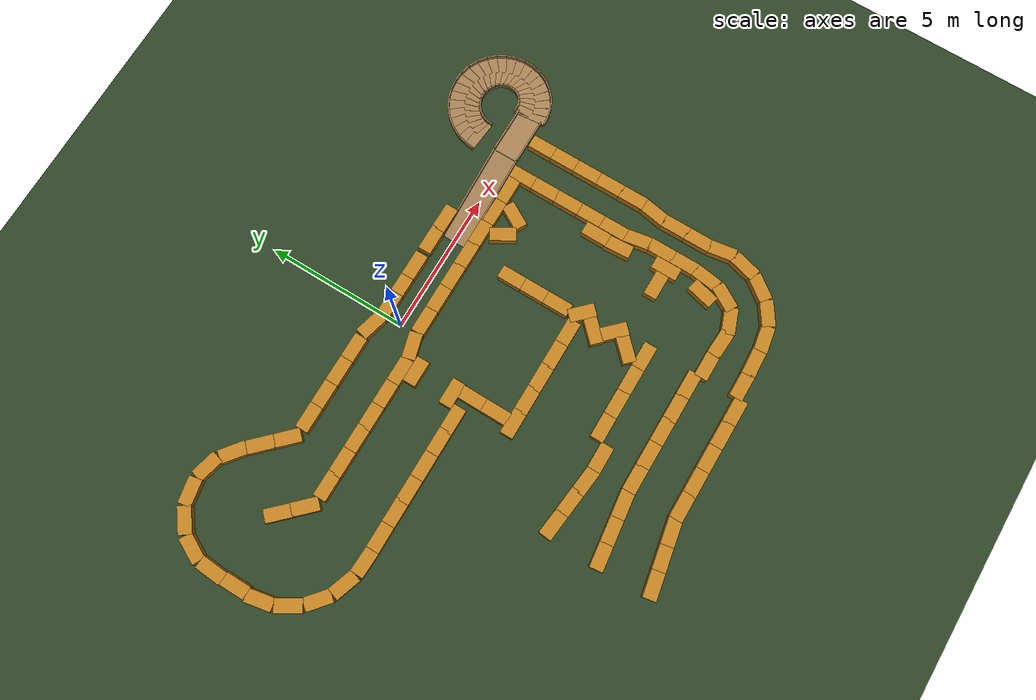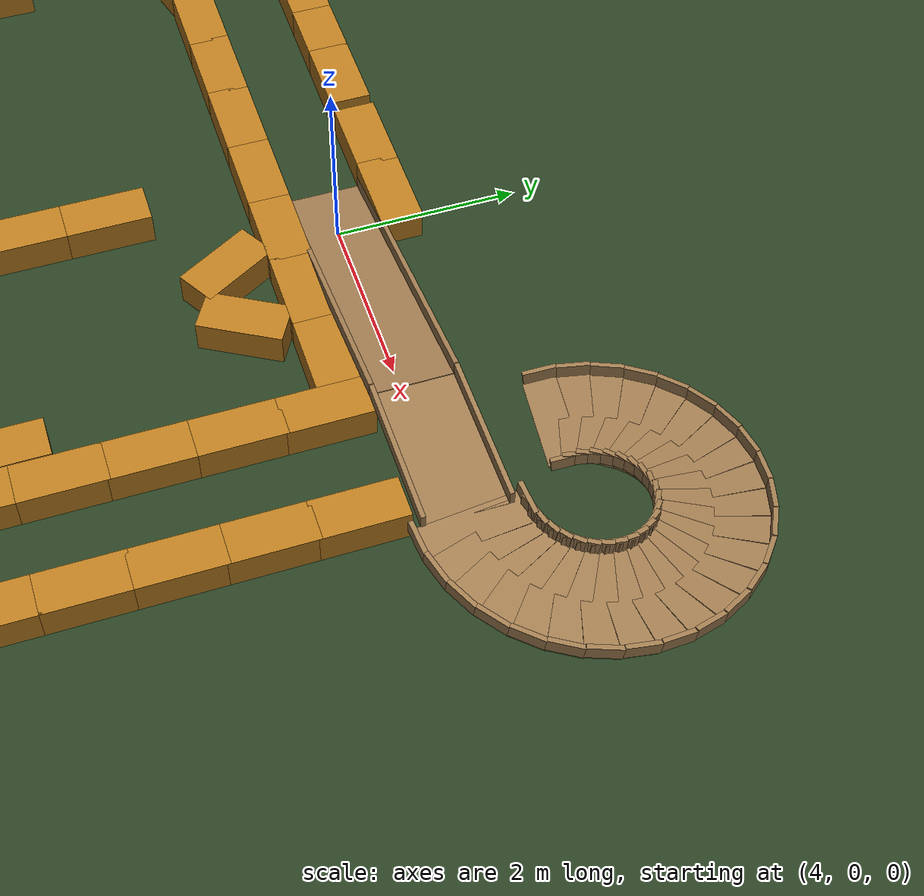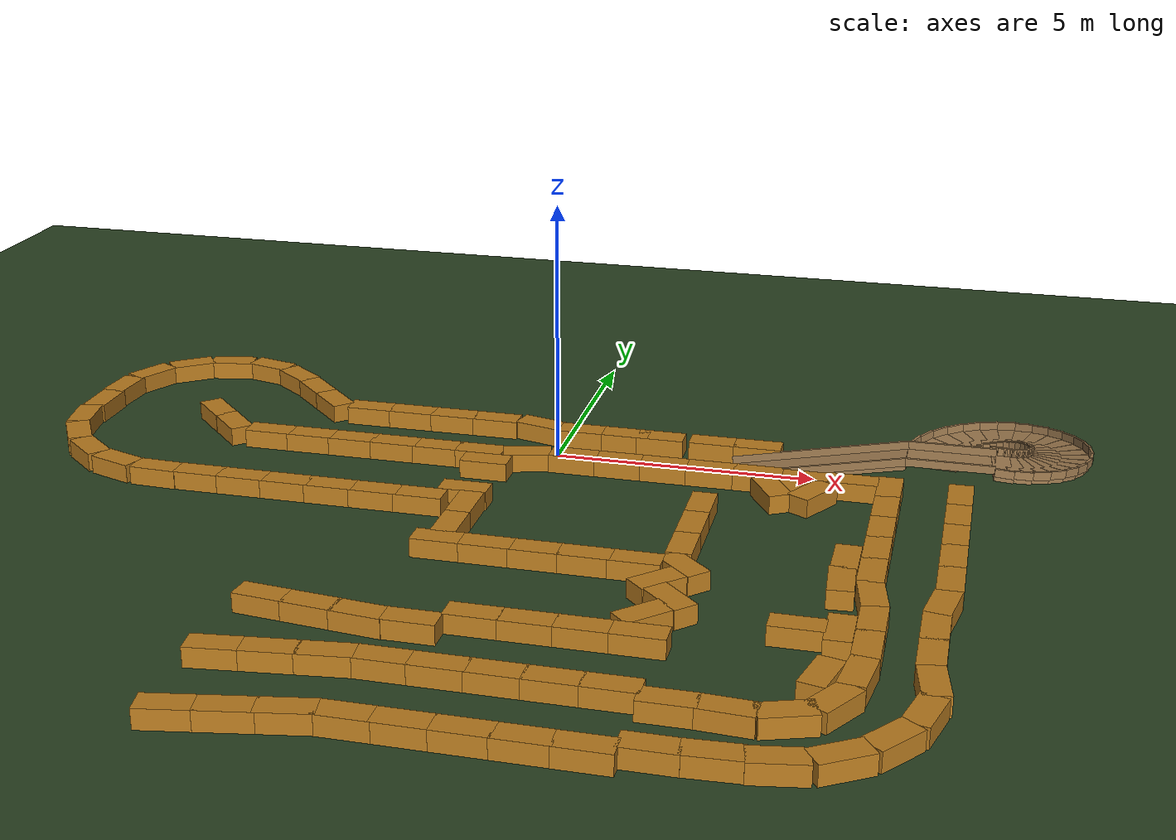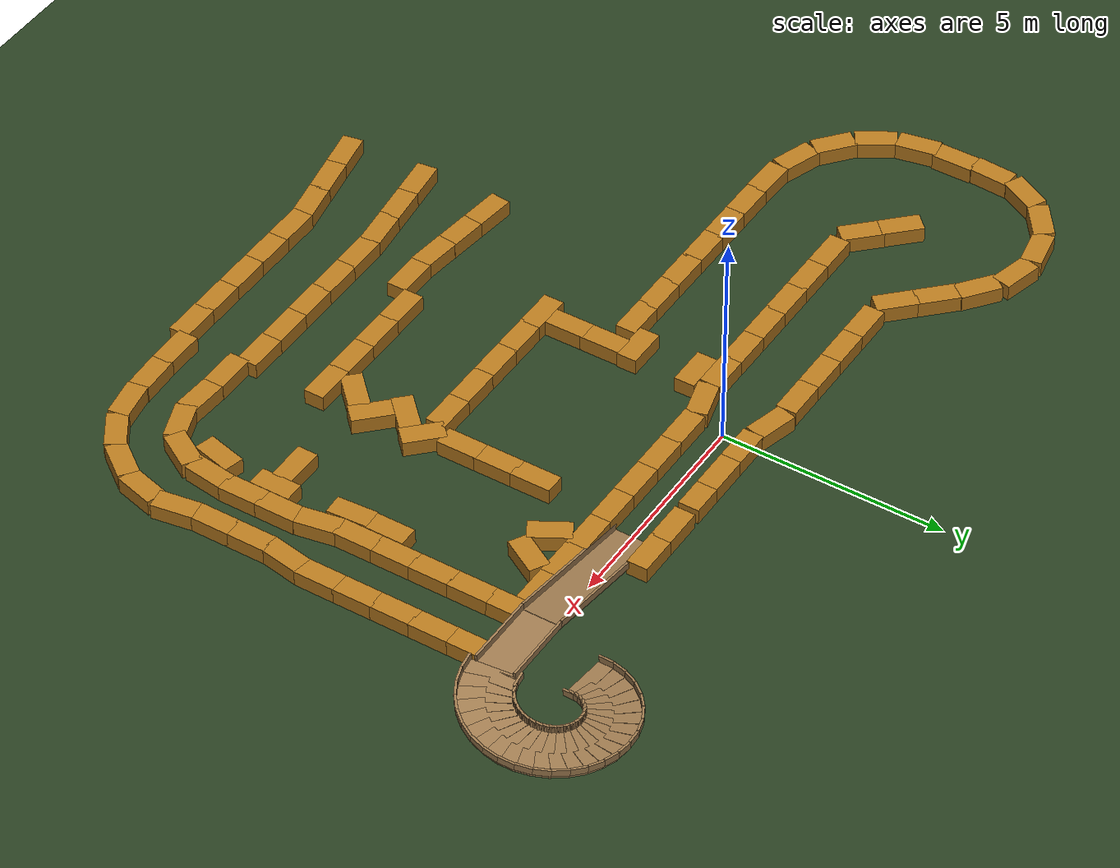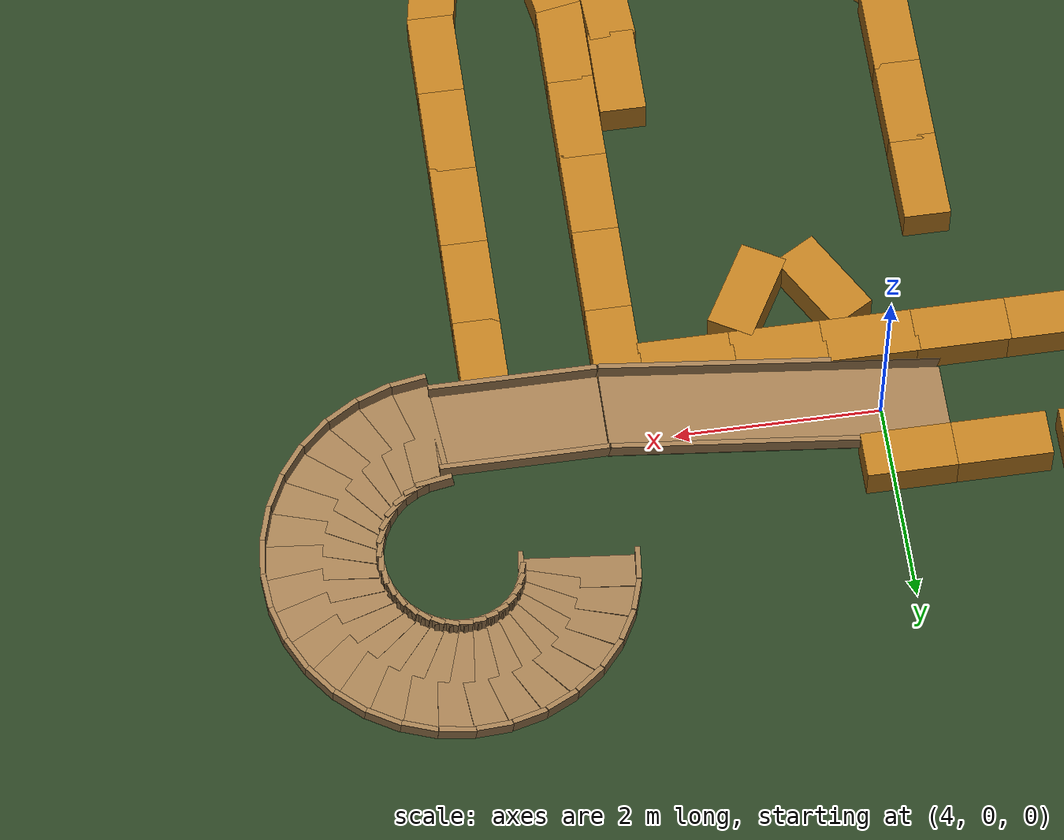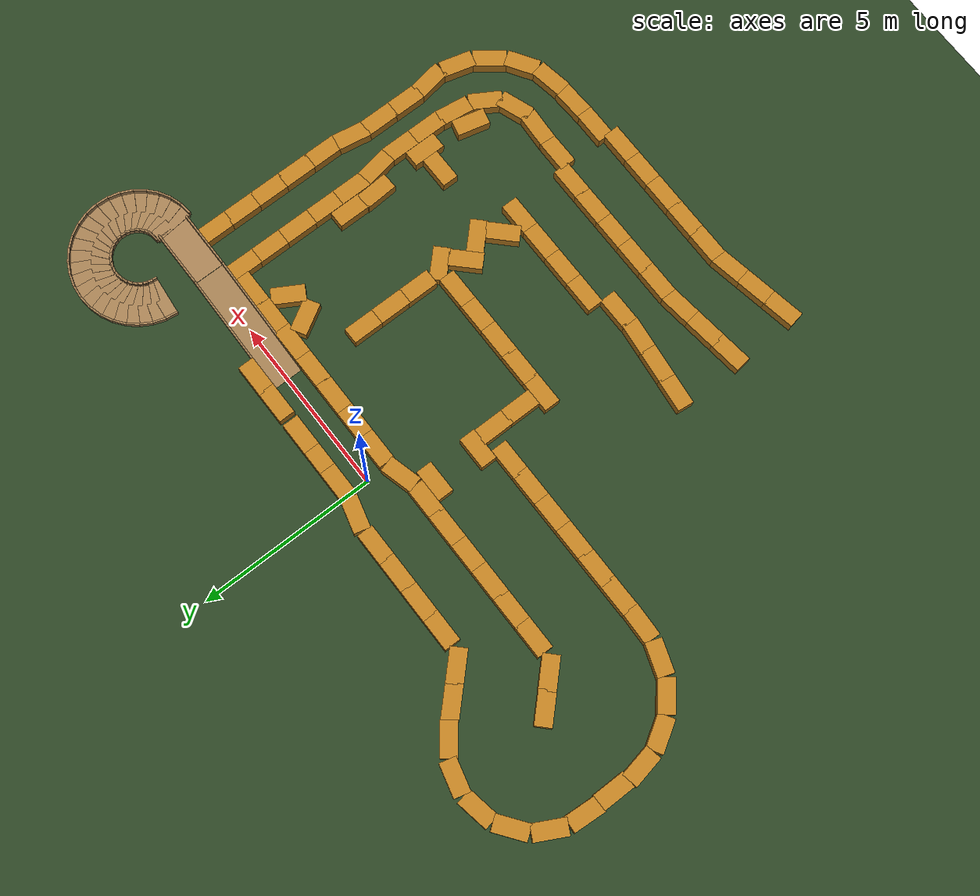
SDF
<sdf version="1.10">
 <world name="cfr_obstacle_course">
  <physics name="1ms" type="ignored">
   <max_step_size>0.001</max_step_size>
   <real_time_factor>1.0</real_time_factor>
  </physics>
  <plugin filename="gz-sim-physics-system" name="gz::sim::systems::Physics"/>
  <plugin filename="gz-sim-user-commands-system" name="gz::sim::systems::UserCommands"/>
  <plugin filename="gz-sim-scene-broadcaster-system" name="gz::sim::systems::SceneBroadcaster"/>
  <plugin filename="gz-sim-contact-system" name="gz::sim::systems::Contact"/>
  <plugin filename="gz-sim-imu-system" name="gz::sim::systems::Imu"/>
  <plugin filename="gz-sim-sensors-system" name="gz::sim::systems::Sensors">
   <render_engine>ogre2</render_engine>
  </plugin>
  <light type="directional" name="sun">
   <pose>0 0 20 0 0 0</pose>
   <diffuse>0.8 0.8 0.8 1</diffuse>
   <specular>0.2 0.2 0.2 1</specular>
   <direction>-0.4 0.2 -0.9</direction>
  </light>
  <model name="ground">
   <static>true</static>
   <pose>0.005 -4.540 0 0 0 0</pose>
   <link name="link">
    <collision name="collision">
     <geometry><plane><normal>0 0 1</normal><size>30 24</size></plane></geometry>
     <surface>
      <friction>
       <ode><mu>50</mu></ode>
       <bullet><friction>1</friction><rolling_friction>0.001</rolling_friction></bullet>
      </friction>
     </surface>
    </collision>
    <visual name="visual">
     <geometry><plane><normal>0 0 1</normal><size>30 24</size></plane></geometry>
     <material><diffuse>0.16 0.25 0.13 1</diffuse></material>
    </visual>
   </link>
  </model>
  <model name="course_bales">
   <static>true</static>
   <link name="link">
    <collision name="bale_0_collision">
     <pose>0.4820 -0.6423 0.1778 0.0000 0.0000 6.2832</pose>
     <geometry><box><size>0.9144 0.4572 0.3556</size></box></geometry>
     <surface>
      <friction>
       <ode><mu>50</mu><mu2>50</mu2></ode>
       <bullet><friction>50</friction><friction2>50</friction2></bullet>
      </friction>
     </surface>
    </collision>
    <visual name="bale_0_visual">
     <pose>0.4820 -0.6423 0.1778 0.0000 0.0000 6.2832</pose>
     <geometry><box><size>0.9144 0.4572 0.3556</size></box></geometry>
     <material><diffuse>0.72 0.48 0.12 1</diffuse></material>
    </visual>
    <collision name="bale_1_collision">
     <pose>1.3663 -0.6423 0.1778 0.0000 0.0000 6.2832</pose>
     <geometry><box><size>0.9144 0.4572 0.3556</size></box></geometry>
     <surface>
      <friction>
       <ode><mu>50</mu><mu2>50</mu2></ode>
       <bullet><friction>50</friction><friction2>50</friction2></bullet>
      </friction>
     </surface>
    </collision>
    <visual name="bale_1_visual">
     <pose>1.3663 -0.6423 0.1778 0.0000 0.0000 6.2832</pose>
     <geometry><box><size>0.9144 0.4572 0.3556</size></box></geometry>
     <material><diffuse>0.72 0.48 0.12 1</diffuse></material>
    </visual>
    <collision name="bale_2_collision">
     <pose>2.2506 -0.6423 0.1778 0.0000 0.0000 6.2832</pose>
     <geometry><box><size>0.9144 0.4572 0.3556</size></box></geometry>
     <surface>
      <friction>
       <ode><mu>50</mu><mu2>50</mu2></ode>
       <bullet><friction>50</friction><friction2>50</friction2></bullet>
      </friction>
     </surface>
    </collision>
    <visual name="bale_2_visual">
     <pose>2.2506 -0.6423 0.1778 0.0000 0.0000 6.2832</pose>
     <geometry><box><size>0.9144 0.4572 0.3556</size></box></geometry>
     <material><diffuse>0.72 0.48 0.12 1</diffuse></material>
    </visual>
    <collision name="bale_3_collision">
     <pose>3.1349 -0.6423 0.1778 0.0000 0.0000 6.2832</pose>
     <geometry><box><size>0.9144 0.4572 0.3556</size></box></geometry>
     <surface>
      <friction>
       <ode><mu>50</mu><mu2>50</mu2></ode>
       <bullet><friction>50</friction><friction2>50</friction2></bullet>
      </friction>
     </surface>
    </collision>
    <visual name="bale_3_visual">
     <pose>3.1349 -0.6423 0.1778 0.0000 0.0000 6.2832</pose>
     <geometry><box><size>0.9144 0.4572 0.3556</size></box></geometry>
     <material><diffuse>0.72 0.48 0.12 1</diffuse></material>
    </visual>
    <collision name="bale_4_collision">
     <pose>4.0192 -0.6423 0.1778 0.0000 0.0000 6.2832</pose>
     <geometry><box><size>0.9144 0.4572 0.3556</size></box></geometry>
     <surface>
      <friction>
       <ode><mu>50</mu><mu2>50</mu2></ode>
       <bullet><friction>50</friction><friction2>50</friction2></bullet>
      </friction>
     </surface>
    </collision>
    <visual name="bale_4_visual">
     <pose>4.0192 -0.6423 0.1778 0.0000 0.0000 6.2832</pose>
     <geometry><box><size>0.9144 0.4572 0.3556</size></box></geometry>
     <material><diffuse>0.72 0.48 0.12 1</diffuse></material>
    </visual>
    <collision name="bale_5_collision">
     <pose>4.9035 -0.6423 0.1778 0.0000 0.0000 6.2832</pose>
     <geometry><box><size>0.9144 0.4572 0.3556</size></box></geometry>
     <surface>
      <friction>
       <ode><mu>50</mu><mu2>50</mu2></ode>
       <bullet><friction>50</friction><friction2>50</friction2></bullet>
      </friction>
     </surface>
    </collision>
    <visual name="bale_5_visual">
     <pose>4.9035 -0.6423 0.1778 0.0000 0.0000 6.2832</pose>
     <geometry><box><size>0.9144 0.4572 0.3556</size></box></geometry>
     <material><diffuse>0.72 0.48 0.12 1</diffuse></material>
    </visual>
    <collision name="bale_6_collision">
     <pose>5.7878 -0.6423 0.1778 0.0000 0.0000 6.2832</pose>
     <geometry><box><size>0.9144 0.4572 0.3556</size></box></geometry>
     <surface>
      <friction>
       <ode><mu>50</mu><mu2>50</mu2></ode>
       <bullet><friction>50</friction><friction2>50</friction2></bullet>
      </friction>
     </surface>
    </collision>
    <visual name="bale_6_visual">
     <pose>5.7878 -0.6423 0.1778 0.0000 0.0000 6.2832</pose>
     <geometry><box><size>0.9144 0.4572 0.3556</size></box></geometry>
     <material><diffuse>0.72 0.48 0.12 1</diffuse></material>
    </visual>
    <collision name="bale_7_collision">
     <pose>-7.1547 0.0042 0.1778 0.0000 0.0000 5.4897</pose>
     <geometry><box><size>0.9144 0.4572 0.3556</size></box></geometry>
     <surface>
      <friction>
       <ode><mu>50</mu><mu2>50</mu2></ode>
       <bullet><friction>50</friction><friction2>50</friction2></bullet>
      </friction>
     </surface>
    </collision>
    <visual name="bale_7_visual">
     <pose>-7.1547 0.0042 0.1778 0.0000 0.0000 5.4897</pose>
     <geometry><box><size>0.9144 0.4572 0.3556</size></box></geometry>
     <material><diffuse>0.72 0.48 0.12 1</diffuse></material>
    </visual>
    <collision name="bale_8_collision">
     <pose>-6.5454 -0.6076 0.1778 0.0000 0.0000 5.4897</pose>
     <geometry><box><size>0.9144 0.4572 0.3556</size></box></geometry>
     <surface>
      <friction>
       <ode><mu>50</mu><mu2>50</mu2></ode>
       <bullet><friction>50</friction><friction2>50</friction2></bullet>
      </friction>
     </surface>
    </collision>
    <visual name="bale_8_visual">
     <pose>-6.5454 -0.6076 0.1778 0.0000 0.0000 5.4897</pose>
     <geometry><box><size>0.9144 0.4572 0.3556</size></box></geometry>
     <material><diffuse>0.72 0.48 0.12 1</diffuse></material>
    </visual>
    <collision name="bale_9_collision">
     <pose>-5.6457 -0.8411 0.1778 0.0000 0.0000 6.2832</pose>
     <geometry><box><size>0.9144 0.4572 0.3556</size></box></geometry>
     <surface>
      <friction>
       <ode><mu>50</mu><mu2>50</mu2></ode>
       <bullet><friction>50</friction><friction2>50</friction2></bullet>
      </friction>
     </surface>
    </collision>
    <visual name="bale_9_visual">
     <pose>-5.6457 -0.8411 0.1778 0.0000 0.0000 6.2832</pose>
     <geometry><box><size>0.9144 0.4572 0.3556</size></box></geometry>
     <material><diffuse>0.72 0.48 0.12 1</diffuse></material>
    </visual>
    <collision name="bale_10_collision">
     <pose>-4.7800 -0.8411 0.1778 0.0000 0.0000 6.2832</pose>
     <geometry><box><size>0.9144 0.4572 0.3556</size></box></geometry>
     <surface>
      <friction>
       <ode><mu>50</mu><mu2>50</mu2></ode>
       <bullet><friction>50</friction><friction2>50</friction2></bullet>
      </friction>
     </surface>
    </collision>
    <visual name="bale_10_visual">
     <pose>-4.7800 -0.8411 0.1778 0.0000 0.0000 6.2832</pose>
     <geometry><box><size>0.9144 0.4572 0.3556</size></box></geometry>
     <material><diffuse>0.72 0.48 0.12 1</diffuse></material>
    </visual>
    <collision name="bale_11_collision">
     <pose>-3.9143 -0.8411 0.1778 0.0000 0.0000 6.2832</pose>
     <geometry><box><size>0.9144 0.4572 0.3556</size></box></geometry>
     <surface>
      <friction>
       <ode><mu>50</mu><mu2>50</mu2></ode>
       <bullet><friction>50</friction><friction2>50</friction2></bullet>
      </friction>
     </surface>
    </collision>
    <visual name="bale_11_visual">
     <pose>-3.9143 -0.8411 0.1778 0.0000 0.0000 6.2832</pose>
     <geometry><box><size>0.9144 0.4572 0.3556</size></box></geometry>
     <material><diffuse>0.72 0.48 0.12 1</diffuse></material>
    </visual>
    <collision name="bale_12_collision">
     <pose>-3.0486 -0.8411 0.1778 0.0000 0.0000 6.2832</pose>
     <geometry><box><size>0.9144 0.4572 0.3556</size></box></geometry>
     <surface>
      <friction>
       <ode><mu>50</mu><mu2>50</mu2></ode>
       <bullet><friction>50</friction><friction2>50</friction2></bullet>
      </friction>
     </surface>
    </collision>
    <visual name="bale_12_visual">
     <pose>-3.0486 -0.8411 0.1778 0.0000 0.0000 6.2832</pose>
     <geometry><box><size>0.9144 0.4572 0.3556</size></box></geometry>
     <material><diffuse>0.72 0.48 0.12 1</diffuse></material>
    </visual>
    <collision name="bale_13_collision">
     <pose>-2.1850 -0.8411 0.1778 0.0000 0.0000 6.2832</pose>
     <geometry><box><size>0.9144 0.4572 0.3556</size></box></geometry>
     <surface>
      <friction>
       <ode><mu>50</mu><mu2>50</mu2></ode>
       <bullet><friction>50</friction><friction2>50</friction2></bullet>
      </friction>
     </surface>
    </collision>
    <visual name="bale_13_visual">
     <pose>-2.1850 -0.8411 0.1778 0.0000 0.0000 6.2832</pose>
     <geometry><box><size>0.9144 0.4572 0.3556</size></box></geometry>
     <material><diffuse>0.72 0.48 0.12 1</diffuse></material>
    </visual>
    <collision name="bale_14_collision">
     <pose>-1.3214 -0.8427 0.1778 0.0000 0.0000 6.2832</pose>
     <geometry><box><size>0.9144 0.4572 0.3556</size></box></geometry>
     <surface>
      <friction>
       <ode><mu>50</mu><mu2>50</mu2></ode>
       <bullet><friction>50</friction><friction2>50</friction2></bullet>
      </friction>
     </surface>
    </collision>
    <visual name="bale_14_visual">
     <pose>-1.3214 -0.8427 0.1778 0.0000 0.0000 6.2832</pose>
     <geometry><box><size>0.9144 0.4572 0.3556</size></box></geometry>
     <material><diffuse>0.72 0.48 0.12 1</diffuse></material>
    </visual>
    <collision name="bale_15_collision">
     <pose>-1.0832 -1.2999 0.1778 0.0000 0.0000 6.2832</pose>
     <geometry><box><size>0.9144 0.4572 0.3556</size></box></geometry>
     <surface>
      <friction>
       <ode><mu>50</mu><mu2>50</mu2></ode>
       <bullet><friction>50</friction><friction2>50</friction2></bullet>
      </friction>
     </surface>
    </collision>
    <visual name="bale_15_visual">
     <pose>-1.0832 -1.2999 0.1778 0.0000 0.0000 6.2832</pose>
     <geometry><box><size>0.9144 0.4572 0.3556</size></box></geometry>
     <material><diffuse>0.72 0.48 0.12 1</diffuse></material>
    </visual>
    <collision name="bale_16_collision">
     <pose>-0.4260 -0.7387 0.1778 0.0000 0.0000 0.2618</pose>
     <geometry><box><size>0.9144 0.4572 0.3556</size></box></geometry>
     <surface>
      <friction>
       <ode><mu>50</mu><mu2>50</mu2></ode>
       <bullet><friction>50</friction><friction2>50</friction2></bullet>
      </friction>
     </surface>
    </collision>
    <visual name="bale_16_visual">
     <pose>-0.4260 -0.7387 0.1778 0.0000 0.0000 0.2618</pose>
     <geometry><box><size>0.9144 0.4572 0.3556</size></box></geometry>
     <material><diffuse>0.72 0.48 0.12 1</diffuse></material>
    </visual>
    <collision name="bale_17_collision">
     <pose>6.5353 -5.2418 0.1778 0.0000 0.0000 1.7453</pose>
     <geometry><box><size>0.9144 0.4572 0.3556</size></box></geometry>
     <surface>
      <friction>
       <ode><mu>50</mu><mu2>50</mu2></ode>
       <bullet><friction>50</friction><friction2>50</friction2></bullet>
      </friction>
     </surface>
    </collision>
    <visual name="bale_17_visual">
     <pose>6.5353 -5.2418 0.1778 0.0000 0.0000 1.7453</pose>
     <geometry><box><size>0.9144 0.4572 0.3556</size></box></geometry>
     <material><diffuse>0.72 0.48 0.12 1</diffuse></material>
    </visual>
    <collision name="bale_18_collision">
     <pose>6.4574 -4.3763 0.1778 0.0000 0.0000 1.5708</pose>
     <geometry><box><size>0.9144 0.4572 0.3556</size></box></geometry>
     <surface>
      <friction>
       <ode><mu>50</mu><mu2>50</mu2></ode>
       <bullet><friction>50</friction><friction2>50</friction2></bullet>
      </friction>
     </surface>
    </collision>
    <visual name="bale_18_visual">
     <pose>6.4574 -4.3763 0.1778 0.0000 0.0000 1.5708</pose>
     <geometry><box><size>0.9144 0.4572 0.3556</size></box></geometry>
     <material><diffuse>0.72 0.48 0.12 1</diffuse></material>
    </visual>
    <collision name="bale_19_collision">
     <pose>6.4574 -3.4920 0.1778 0.0000 0.0000 1.5708</pose>
     <geometry><box><size>0.9144 0.4572 0.3556</size></box></geometry>
     <surface>
      <friction>
       <ode><mu>50</mu><mu2>50</mu2></ode>
       <bullet><friction>50</friction><friction2>50</friction2></bullet>
      </friction>
     </surface>
    </collision>
    <visual name="bale_19_visual">
     <pose>6.4574 -3.4920 0.1778 0.0000 0.0000 1.5708</pose>
     <geometry><box><size>0.9144 0.4572 0.3556</size></box></geometry>
     <material><diffuse>0.72 0.48 0.12 1</diffuse></material>
    </visual>
    <collision name="bale_20_collision">
     <pose>6.4574 -2.6077 0.1778 0.0000 0.0000 1.5708</pose>
     <geometry><box><size>0.9144 0.4572 0.3556</size></box></geometry>
     <surface>
      <friction>
       <ode><mu>50</mu><mu2>50</mu2></ode>
       <bullet><friction>50</friction><friction2>50</friction2></bullet>
      </friction>
     </surface>
    </collision>
    <visual name="bale_20_visual">
     <pose>6.4574 -2.6077 0.1778 0.0000 0.0000 1.5708</pose>
     <geometry><box><size>0.9144 0.4572 0.3556</size></box></geometry>
     <material><diffuse>0.72 0.48 0.12 1</diffuse></material>
    </visual>
    <collision name="bale_21_collision">
     <pose>6.4574 -1.7234 0.1778 0.0000 0.0000 1.5708</pose>
     <geometry><box><size>0.9144 0.4572 0.3556</size></box></geometry>
     <surface>
      <friction>
       <ode><mu>50</mu><mu2>50</mu2></ode>
       <bullet><friction>50</friction><friction2>50</friction2></bullet>
      </friction>
     </surface>
    </collision>
    <visual name="bale_21_visual">
     <pose>6.4574 -1.7234 0.1778 0.0000 0.0000 1.5708</pose>
     <geometry><box><size>0.9144 0.4572 0.3556</size></box></geometry>
     <material><diffuse>0.72 0.48 0.12 1</diffuse></material>
    </visual>
    <collision name="bale_22_collision">
     <pose>6.4574 -0.8391 0.1778 0.0000 0.0000 1.5708</pose>
     <geometry><box><size>0.9144 0.4572 0.3556</size></box></geometry>
     <surface>
      <friction>
       <ode><mu>50</mu><mu2>50</mu2></ode>
       <bullet><friction>50</friction><friction2>50</friction2></bullet>
      </friction>
     </surface>
    </collision>
    <visual name="bale_22_visual">
     <pose>6.4574 -0.8391 0.1778 0.0000 0.0000 1.5708</pose>
     <geometry><box><size>0.9144 0.4572 0.3556</size></box></geometry>
     <material><diffuse>0.72 0.48 0.12 1</diffuse></material>
    </visual>
    <collision name="bale_23_collision">
     <pose>6.2859 -8.6786 0.1778 0.0000 0.0000 1.0315</pose>
     <geometry><box><size>0.9144 0.4572 0.3556</size></box></geometry>
     <surface>
      <friction>
       <ode><mu>50</mu><mu2>50</mu2></ode>
       <bullet><friction>50</friction><friction2>50</friction2></bullet>
      </friction>
     </surface>
    </collision>
    <visual name="bale_23_visual">
     <pose>6.2859 -8.6786 0.1778 0.0000 0.0000 1.0315</pose>
     <geometry><box><size>0.9144 0.4572 0.3556</size></box></geometry>
     <material><diffuse>0.72 0.48 0.12 1</diffuse></material>
    </visual>
    <collision name="bale_24_collision">
     <pose>6.5526 -7.8425 0.1778 0.0000 0.0000 1.4318</pose>
     <geometry><box><size>0.9144 0.4572 0.3556</size></box></geometry>
     <surface>
      <friction>
       <ode><mu>50</mu><mu2>50</mu2></ode>
       <bullet><friction>50</friction><friction2>50</friction2></bullet>
      </friction>
     </surface>
    </collision>
    <visual name="bale_24_visual">
     <pose>6.5526 -7.8425 0.1778 0.0000 0.0000 1.4318</pose>
     <geometry><box><size>0.9144 0.4572 0.3556</size></box></geometry>
     <material><diffuse>0.72 0.48 0.12 1</diffuse></material>
    </visual>
    <collision name="bale_25_collision">
     <pose>5.6700 -9.1918 0.1778 0.0000 0.0000 0.3509</pose>
     <geometry><box><size>0.9144 0.4572 0.3556</size></box></geometry>
     <surface>
      <friction>
       <ode><mu>50</mu><mu2>50</mu2></ode>
       <bullet><friction>50</friction><friction2>50</friction2></bullet>
      </friction>
     </surface>
    </collision>
    <visual name="bale_25_visual">
     <pose>5.6700 -9.1918 0.1778 0.0000 0.0000 0.3509</pose>
     <geometry><box><size>0.9144 0.4572 0.3556</size></box></geometry>
     <material><diffuse>0.72 0.48 0.12 1</diffuse></material>
    </visual>
    <collision name="bale_26_collision">
     <pose>4.8384 -9.2976 0.1778 0.0000 0.0000 6.2256</pose>
     <geometry><box><size>0.9144 0.4572 0.3556</size></box></geometry>
     <surface>
      <friction>
       <ode><mu>50</mu><mu2>50</mu2></ode>
       <bullet><friction>50</friction><friction2>50</friction2></bullet>
      </friction>
     </surface>
    </collision>
    <visual name="bale_26_visual">
     <pose>4.8384 -9.2976 0.1778 0.0000 0.0000 6.2256</pose>
     <geometry><box><size>0.9144 0.4572 0.3556</size></box></geometry>
     <material><diffuse>0.72 0.48 0.12 1</diffuse></material>
    </visual>
    <collision name="bale_27_collision">
     <pose>6.6149 -6.9768 0.1778 0.0000 0.0000 1.5708</pose>
     <geometry><box><size>0.9144 0.4572 0.3556</size></box></geometry>
     <surface>
      <friction>
       <ode><mu>50</mu><mu2>50</mu2></ode>
       <bullet><friction>50</friction><friction2>50</friction2></bullet>
      </friction>
     </surface>
    </collision>
    <visual name="bale_27_visual">
     <pose>6.6149 -6.9768 0.1778 0.0000 0.0000 1.5708</pose>
     <geometry><box><size>0.9144 0.4572 0.3556</size></box></geometry>
     <material><diffuse>0.72 0.48 0.12 1</diffuse></material>
    </visual>
    <collision name="bale_28_collision">
     <pose>6.6149 -6.1132 0.1778 0.0000 0.0000 1.5708</pose>
     <geometry><box><size>0.9144 0.4572 0.3556</size></box></geometry>
     <surface>
      <friction>
       <ode><mu>50</mu><mu2>50</mu2></ode>
       <bullet><friction>50</friction><friction2>50</friction2></bullet>
      </friction>
     </surface>
    </collision>
    <visual name="bale_28_visual">
     <pose>6.6149 -6.1132 0.1778 0.0000 0.0000 1.5708</pose>
     <geometry><box><size>0.9144 0.4572 0.3556</size></box></geometry>
     <material><diffuse>0.72 0.48 0.12 1</diffuse></material>
    </visual>
    <collision name="bale_29_collision">
     <pose>3.9745 -9.2717 0.1778 0.0000 0.0000 6.2832</pose>
     <geometry><box><size>0.9144 0.4572 0.3556</size></box></geometry>
     <surface>
      <friction>
       <ode><mu>50</mu><mu2>50</mu2></ode>
       <bullet><friction>50</friction><friction2>50</friction2></bullet>
      </friction>
     </surface>
    </collision>
    <visual name="bale_29_visual">
     <pose>3.9745 -9.2717 0.1778 0.0000 0.0000 6.2832</pose>
     <geometry><box><size>0.9144 0.4572 0.3556</size></box></geometry>
     <material><diffuse>0.72 0.48 0.12 1</diffuse></material>
    </visual>
    <collision name="bale_30_collision">
     <pose>3.1095 -9.0682 0.1778 0.0000 0.0000 6.2832</pose>
     <geometry><box><size>0.9144 0.4572 0.3556</size></box></geometry>
     <surface>
      <friction>
       <ode><mu>50</mu><mu2>50</mu2></ode>
       <bullet><friction>50</friction><friction2>50</friction2></bullet>
      </friction>
     </surface>
    </collision>
    <visual name="bale_30_visual">
     <pose>3.1095 -9.0682 0.1778 0.0000 0.0000 6.2832</pose>
     <geometry><box><size>0.9144 0.4572 0.3556</size></box></geometry>
     <material><diffuse>0.72 0.48 0.12 1</diffuse></material>
    </visual>
    <collision name="bale_31_collision">
     <pose>2.2294 -9.0672 0.1778 0.0000 0.0000 6.2832</pose>
     <geometry><box><size>0.9144 0.4572 0.3556</size></box></geometry>
     <surface>
      <friction>
       <ode><mu>50</mu><mu2>50</mu2></ode>
       <bullet><friction>50</friction><friction2>50</friction2></bullet>
      </friction>
     </surface>
    </collision>
    <visual name="bale_31_visual">
     <pose>2.2294 -9.0672 0.1778 0.0000 0.0000 6.2832</pose>
     <geometry><box><size>0.9144 0.4572 0.3556</size></box></geometry>
     <material><diffuse>0.72 0.48 0.12 1</diffuse></material>
    </visual>
    <collision name="bale_32_collision">
     <pose>1.3494 -9.0672 0.1778 0.0000 0.0000 6.2832</pose>
     <geometry><box><size>0.9144 0.4572 0.3556</size></box></geometry>
     <surface>
      <friction>
       <ode><mu>50</mu><mu2>50</mu2></ode>
       <bullet><friction>50</friction><friction2>50</friction2></bullet>
      </friction>
     </surface>
    </collision>
    <visual name="bale_32_visual">
     <pose>1.3494 -9.0672 0.1778 0.0000 0.0000 6.2832</pose>
     <geometry><box><size>0.9144 0.4572 0.3556</size></box></geometry>
     <material><diffuse>0.72 0.48 0.12 1</diffuse></material>
    </visual>
    <collision name="bale_33_collision">
     <pose>0.4693 -9.0672 0.1778 0.0000 0.0000 6.2832</pose>
     <geometry><box><size>0.9144 0.4572 0.3556</size></box></geometry>
     <surface>
      <friction>
       <ode><mu>50</mu><mu2>50</mu2></ode>
       <bullet><friction>50</friction><friction2>50</friction2></bullet>
      </friction>
     </surface>
    </collision>
    <visual name="bale_33_visual">
     <pose>0.4693 -9.0672 0.1778 0.0000 0.0000 6.2832</pose>
     <geometry><box><size>0.9144 0.4572 0.3556</size></box></geometry>
     <material><diffuse>0.72 0.48 0.12 1</diffuse></material>
    </visual>
    <collision name="bale_34_collision">
     <pose>-0.3947 -7.7930 0.1778 0.0000 0.0000 6.2832</pose>
     <geometry><box><size>0.9144 0.4572 0.3556</size></box></geometry>
     <surface>
      <friction>
       <ode><mu>50</mu><mu2>50</mu2></ode>
       <bullet><friction>50</friction><friction2>50</friction2></bullet>
      </friction>
     </surface>
    </collision>
    <visual name="bale_34_visual">
     <pose>-0.3947 -7.7930 0.1778 0.0000 0.0000 6.2832</pose>
     <geometry><box><size>0.9144 0.4572 0.3556</size></box></geometry>
     <material><diffuse>0.72 0.48 0.12 1</diffuse></material>
    </visual>
    <collision name="bale_35_collision">
     <pose>2.2812 -7.3832 0.1778 0.0000 0.0000 6.2832</pose>
     <geometry><box><size>0.9144 0.4572 0.3556</size></box></geometry>
     <surface>
      <friction>
       <ode><mu>50</mu><mu2>50</mu2></ode>
       <bullet><friction>50</friction><friction2>50</friction2></bullet>
      </friction>
     </surface>
    </collision>
    <visual name="bale_35_visual">
     <pose>2.2812 -7.3832 0.1778 0.0000 0.0000 6.2832</pose>
     <geometry><box><size>0.9144 0.4572 0.3556</size></box></geometry>
     <material><diffuse>0.72 0.48 0.12 1</diffuse></material>
    </visual>
    <collision name="bale_36_collision">
     <pose>1.3880 -7.3832 0.1778 0.0000 0.0000 6.2832</pose>
     <geometry><box><size>0.9144 0.4572 0.3556</size></box></geometry>
     <surface>
      <friction>
       <ode><mu>50</mu><mu2>50</mu2></ode>
       <bullet><friction>50</friction><friction2>50</friction2></bullet>
      </friction>
     </surface>
    </collision>
    <visual name="bale_36_visual">
     <pose>1.3880 -7.3832 0.1778 0.0000 0.0000 6.2832</pose>
     <geometry><box><size>0.9144 0.4572 0.3556</size></box></geometry>
     <material><diffuse>0.72 0.48 0.12 1</diffuse></material>
    </visual>
    <collision name="bale_37_collision">
     <pose>0.4947 -7.3832 0.1778 0.0000 0.0000 6.2832</pose>
     <geometry><box><size>0.9144 0.4572 0.3556</size></box></geometry>
     <surface>
      <friction>
       <ode><mu>50</mu><mu2>50</mu2></ode>
       <bullet><friction>50</friction><friction2>50</friction2></bullet>
      </friction>
     </surface>
    </collision>
    <visual name="bale_37_visual">
     <pose>0.4947 -7.3832 0.1778 0.0000 0.0000 6.2832</pose>
     <geometry><box><size>0.9144 0.4572 0.3556</size></box></geometry>
     <material><diffuse>0.72 0.48 0.12 1</diffuse></material>
    </visual>
    <collision name="bale_38_collision">
     <pose>-0.4068 -9.0672 0.1778 0.0000 0.0000 6.2832</pose>
     <geometry><box><size>0.9144 0.4572 0.3556</size></box></geometry>
     <surface>
      <friction>
       <ode><mu>50</mu><mu2>50</mu2></ode>
       <bullet><friction>50</friction><friction2>50</friction2></bullet>
      </friction>
     </surface>
    </collision>
    <visual name="bale_38_visual">
     <pose>-0.4068 -9.0672 0.1778 0.0000 0.0000 6.2832</pose>
     <geometry><box><size>0.9144 0.4572 0.3556</size></box></geometry>
     <material><diffuse>0.72 0.48 0.12 1</diffuse></material>
    </visual>
    <collision name="bale_39_collision">
     <pose>3.1744 -7.3832 0.1778 0.0000 0.0000 6.2832</pose>
     <geometry><box><size>0.9144 0.4572 0.3556</size></box></geometry>
     <surface>
      <friction>
       <ode><mu>50</mu><mu2>50</mu2></ode>
       <bullet><friction>50</friction><friction2>50</friction2></bullet>
      </friction>
     </surface>
    </collision>
    <visual name="bale_39_visual">
     <pose>3.1744 -7.3832 0.1778 0.0000 0.0000 6.2832</pose>
     <geometry><box><size>0.9144 0.4572 0.3556</size></box></geometry>
     <material><diffuse>0.72 0.48 0.12 1</diffuse></material>
    </visual>
    <collision name="bale_40_collision">
     <pose>-1.3014 -9.1204 0.1778 0.0000 0.0000 0.1193</pose>
     <geometry><box><size>0.9144 0.4572 0.3556</size></box></geometry>
     <surface>
      <friction>
       <ode><mu>50</mu><mu2>50</mu2></ode>
       <bullet><friction>50</friction><friction2>50</friction2></bullet>
      </friction>
     </surface>
    </collision>
    <visual name="bale_40_visual">
     <pose>-1.3014 -9.1204 0.1778 0.0000 0.0000 0.1193</pose>
     <geometry><box><size>0.9144 0.4572 0.3556</size></box></geometry>
     <material><diffuse>0.72 0.48 0.12 1</diffuse></material>
    </visual>
    <collision name="bale_41_collision">
     <pose>-2.1625 -9.2236 0.1778 0.0000 0.0000 0.1193</pose>
     <geometry><box><size>0.9144 0.4572 0.3556</size></box></geometry>
     <surface>
      <friction>
       <ode><mu>50</mu><mu2>50</mu2></ode>
       <bullet><friction>50</friction><friction2>50</friction2></bullet>
      </friction>
     </surface>
    </collision>
    <visual name="bale_41_visual">
     <pose>-2.1625 -9.2236 0.1778 0.0000 0.0000 0.1193</pose>
     <geometry><box><size>0.9144 0.4572 0.3556</size></box></geometry>
     <material><diffuse>0.72 0.48 0.12 1</diffuse></material>
    </visual>
    <collision name="bale_42_collision">
     <pose>-3.0237 -9.3268 0.1778 0.0000 0.0000 0.1193</pose>
     <geometry><box><size>0.9144 0.4572 0.3556</size></box></geometry>
     <surface>
      <friction>
       <ode><mu>50</mu><mu2>50</mu2></ode>
       <bullet><friction>50</friction><friction2>50</friction2></bullet>
      </friction>
     </surface>
    </collision>
    <visual name="bale_42_visual">
     <pose>-3.0237 -9.3268 0.1778 0.0000 0.0000 0.1193</pose>
     <geometry><box><size>0.9144 0.4572 0.3556</size></box></geometry>
     <material><diffuse>0.72 0.48 0.12 1</diffuse></material>
    </visual>
    <collision name="bale_43_collision">
     <pose>-1.2633 -7.7560 0.1778 0.0000 0.0000 6.1721</pose>
     <geometry><box><size>0.9144 0.4572 0.3556</size></box></geometry>
     <surface>
      <friction>
       <ode><mu>50</mu><mu2>50</mu2></ode>
       <bullet><friction>50</friction><friction2>50</friction2></bullet>
      </friction>
     </surface>
    </collision>
    <visual name="bale_43_visual">
     <pose>-1.2633 -7.7560 0.1778 0.0000 0.0000 6.1721</pose>
     <geometry><box><size>0.9144 0.4572 0.3556</size></box></geometry>
     <material><diffuse>0.72 0.48 0.12 1</diffuse></material>
    </visual>
    <collision name="bale_44_collision">
     <pose>-2.1221 -7.6586 0.1778 0.0000 0.0000 6.1721</pose>
     <geometry><box><size>0.9144 0.4572 0.3556</size></box></geometry>
     <surface>
      <friction>
       <ode><mu>50</mu><mu2>50</mu2></ode>
       <bullet><friction>50</friction><friction2>50</friction2></bullet>
      </friction>
     </surface>
    </collision>
    <visual name="bale_44_visual">
     <pose>-2.1221 -7.6586 0.1778 0.0000 0.0000 6.1721</pose>
     <geometry><box><size>0.9144 0.4572 0.3556</size></box></geometry>
     <material><diffuse>0.72 0.48 0.12 1</diffuse></material>
    </visual>
    <collision name="bale_45_collision">
     <pose>-2.9793 -7.5613 0.1778 0.0000 0.0000 6.1721</pose>
     <geometry><box><size>0.9144 0.4572 0.3556</size></box></geometry>
     <surface>
      <friction>
       <ode><mu>50</mu><mu2>50</mu2></ode>
       <bullet><friction>50</friction><friction2>50</friction2></bullet>
      </friction>
     </surface>
    </collision>
    <visual name="bale_45_visual">
     <pose>-2.9793 -7.5613 0.1778 0.0000 0.0000 6.1721</pose>
     <geometry><box><size>0.9144 0.4572 0.3556</size></box></geometry>
     <material><diffuse>0.72 0.48 0.12 1</diffuse></material>
    </visual>
    <collision name="bale_46_collision">
     <pose>-1.2449 -10.8322 0.1778 0.0000 0.0000 0.1829</pose>
     <geometry><box><size>0.9144 0.4572 0.3556</size></box></geometry>
     <surface>
      <friction>
       <ode><mu>50</mu><mu2>50</mu2></ode>
       <bullet><friction>50</friction><friction2>50</friction2></bullet>
      </friction>
     </surface>
    </collision>
    <visual name="bale_46_visual">
     <pose>-1.2449 -10.8322 0.1778 0.0000 0.0000 0.1829</pose>
     <geometry><box><size>0.9144 0.4572 0.3556</size></box></geometry>
     <material><diffuse>0.72 0.48 0.12 1</diffuse></material>
    </visual>
    <collision name="bale_47_collision">
     <pose>-2.0978 -10.9900 0.1778 0.0000 0.0000 0.1829</pose>
     <geometry><box><size>0.9144 0.4572 0.3556</size></box></geometry>
     <surface>
      <friction>
       <ode><mu>50</mu><mu2>50</mu2></ode>
       <bullet><friction>50</friction><friction2>50</friction2></bullet>
      </friction>
     </surface>
    </collision>
    <visual name="bale_47_visual">
     <pose>-2.0978 -10.9900 0.1778 0.0000 0.0000 0.1829</pose>
     <geometry><box><size>0.9144 0.4572 0.3556</size></box></geometry>
     <material><diffuse>0.72 0.48 0.12 1</diffuse></material>
    </visual>
    <collision name="bale_48_collision">
     <pose>-2.9507 -11.1477 0.1778 0.0000 0.0000 0.1829</pose>
     <geometry><box><size>0.9144 0.4572 0.3556</size></box></geometry>
     <surface>
      <friction>
       <ode><mu>50</mu><mu2>50</mu2></ode>
       <bullet><friction>50</friction><friction2>50</friction2></bullet>
      </friction>
     </surface>
    </collision>
    <visual name="bale_48_visual">
     <pose>-2.9507 -11.1477 0.1778 0.0000 0.0000 0.1829</pose>
     <geometry><box><size>0.9144 0.4572 0.3556</size></box></geometry>
     <material><diffuse>0.72 0.48 0.12 1</diffuse></material>
    </visual>
    <collision name="bale_49_collision">
     <pose>3.1109 -10.7529 0.1778 0.0000 0.0000 6.2832</pose>
     <geometry><box><size>0.9144 0.4572 0.3556</size></box></geometry>
     <surface>
      <friction>
       <ode><mu>50</mu><mu2>50</mu2></ode>
       <bullet><friction>50</friction><friction2>50</friction2></bullet>
      </friction>
     </surface>
    </collision>
    <visual name="bale_49_visual">
     <pose>3.1109 -10.7529 0.1778 0.0000 0.0000 6.2832</pose>
     <geometry><box><size>0.9144 0.4572 0.3556</size></box></geometry>
     <material><diffuse>0.72 0.48 0.12 1</diffuse></material>
    </visual>
    <collision name="bale_50_collision">
     <pose>2.2346 -10.7518 0.1778 0.0000 0.0000 6.2832</pose>
     <geometry><box><size>0.9144 0.4572 0.3556</size></box></geometry>
     <surface>
      <friction>
       <ode><mu>50</mu><mu2>50</mu2></ode>
       <bullet><friction>50</friction><friction2>50</friction2></bullet>
      </friction>
     </surface>
    </collision>
    <visual name="bale_50_visual">
     <pose>2.2346 -10.7518 0.1778 0.0000 0.0000 6.2832</pose>
     <geometry><box><size>0.9144 0.4572 0.3556</size></box></geometry>
     <material><diffuse>0.72 0.48 0.12 1</diffuse></material>
    </visual>
    <collision name="bale_51_collision">
     <pose>1.3583 -10.7518 0.1778 0.0000 0.0000 6.2832</pose>
     <geometry><box><size>0.9144 0.4572 0.3556</size></box></geometry>
     <surface>
      <friction>
       <ode><mu>50</mu><mu2>50</mu2></ode>
       <bullet><friction>50</friction><friction2>50</friction2></bullet>
      </friction>
     </surface>
    </collision>
    <visual name="bale_51_visual">
     <pose>1.3583 -10.7518 0.1778 0.0000 0.0000 6.2832</pose>
     <geometry><box><size>0.9144 0.4572 0.3556</size></box></geometry>
     <material><diffuse>0.72 0.48 0.12 1</diffuse></material>
    </visual>
    <collision name="bale_52_collision">
     <pose>0.4820 -10.7518 0.1778 0.0000 0.0000 6.2832</pose>
     <geometry><box><size>0.9144 0.4572 0.3556</size></box></geometry>
     <surface>
      <friction>
       <ode><mu>50</mu><mu2>50</mu2></ode>
       <bullet><friction>50</friction><friction2>50</friction2></bullet>
      </friction>
     </surface>
    </collision>
    <visual name="bale_52_visual">
     <pose>0.4820 -10.7518 0.1778 0.0000 0.0000 6.2832</pose>
     <geometry><box><size>0.9144 0.4572 0.3556</size></box></geometry>
     <material><diffuse>0.72 0.48 0.12 1</diffuse></material>
    </visual>
    <collision name="bale_53_collision">
     <pose>-0.3943 -10.7519 0.1778 0.0000 0.0000 6.2832</pose>
     <geometry><box><size>0.9144 0.4572 0.3556</size></box></geometry>
     <surface>
      <friction>
       <ode><mu>50</mu><mu2>50</mu2></ode>
       <bullet><friction>50</friction><friction2>50</friction2></bullet>
      </friction>
     </surface>
    </collision>
    <visual name="bale_53_visual">
     <pose>-0.3943 -10.7519 0.1778 0.0000 0.0000 6.2832</pose>
     <geometry><box><size>0.9144 0.4572 0.3556</size></box></geometry>
     <material><diffuse>0.72 0.48 0.12 1</diffuse></material>
    </visual>
    <collision name="bale_54_collision">
     <pose>7.6529 -5.2573 0.1778 0.0000 0.0000 1.3963</pose>
     <geometry><box><size>0.9144 0.4572 0.3556</size></box></geometry>
     <surface>
      <friction>
       <ode><mu>50</mu><mu2>50</mu2></ode>
       <bullet><friction>50</friction><friction2>50</friction2></bullet>
      </friction>
     </surface>
    </collision>
    <visual name="bale_54_visual">
     <pose>7.6529 -5.2573 0.1778 0.0000 0.0000 1.3963</pose>
     <geometry><box><size>0.9144 0.4572 0.3556</size></box></geometry>
     <material><diffuse>0.72 0.48 0.12 1</diffuse></material>
    </visual>
    <collision name="bale_55_collision">
     <pose>6.5399 -10.1264 0.1778 0.0000 0.0000 0.5742</pose>
     <geometry><box><size>0.9144 0.4572 0.3556</size></box></geometry>
     <surface>
      <friction>
       <ode><mu>50</mu><mu2>50</mu2></ode>
       <bullet><friction>50</friction><friction2>50</friction2></bullet>
      </friction>
     </surface>
    </collision>
    <visual name="bale_55_visual">
     <pose>6.5399 -10.1264 0.1778 0.0000 0.0000 0.5742</pose>
     <geometry><box><size>0.9144 0.4572 0.3556</size></box></geometry>
     <material><diffuse>0.72 0.48 0.12 1</diffuse></material>
    </visual>
    <collision name="bale_56_collision">
     <pose>7.1792 -9.5174 0.1778 0.0000 0.0000 0.9250</pose>
     <geometry><box><size>0.9144 0.4572 0.3556</size></box></geometry>
     <surface>
      <friction>
       <ode><mu>50</mu><mu2>50</mu2></ode>
       <bullet><friction>50</friction><friction2>50</friction2></bullet>
      </friction>
     </surface>
    </collision>
    <visual name="bale_56_visual">
     <pose>7.1792 -9.5174 0.1778 0.0000 0.0000 0.9250</pose>
     <geometry><box><size>0.9144 0.4572 0.3556</size></box></geometry>
     <material><diffuse>0.72 0.48 0.12 1</diffuse></material>
    </visual>
    <collision name="bale_57_collision">
     <pose>5.7194 -10.4439 0.1778 0.0000 0.0000 0.1745</pose>
     <geometry><box><size>0.9144 0.4572 0.3556</size></box></geometry>
     <surface>
      <friction>
       <ode><mu>50</mu><mu2>50</mu2></ode>
       <bullet><friction>50</friction><friction2>50</friction2></bullet>
      </friction>
     </surface>
    </collision>
    <visual name="bale_57_visual">
     <pose>5.7194 -10.4439 0.1778 0.0000 0.0000 0.1745</pose>
     <geometry><box><size>0.9144 0.4572 0.3556</size></box></geometry>
     <material><diffuse>0.72 0.48 0.12 1</diffuse></material>
    </visual>
    <collision name="bale_58_collision">
     <pose>4.8381 -10.5232 0.1778 0.0000 0.0000 0.0524</pose>
     <geometry><box><size>0.9144 0.4572 0.3556</size></box></geometry>
     <surface>
      <friction>
       <ode><mu>50</mu><mu2>50</mu2></ode>
       <bullet><friction>50</friction><friction2>50</friction2></bullet>
      </friction>
     </surface>
    </collision>
    <visual name="bale_58_visual">
     <pose>4.8381 -10.5232 0.1778 0.0000 0.0000 0.0524</pose>
     <geometry><box><size>0.9144 0.4572 0.3556</size></box></geometry>
     <material><diffuse>0.72 0.48 0.12 1</diffuse></material>
    </visual>
    <collision name="bale_59_collision">
     <pose>7.5813 -6.9895 0.1778 0.0000 0.0000 1.5708</pose>
     <geometry><box><size>0.9144 0.4572 0.3556</size></box></geometry>
     <surface>
      <friction>
       <ode><mu>50</mu><mu2>50</mu2></ode>
       <bullet><friction>50</friction><friction2>50</friction2></bullet>
      </friction>
     </surface>
    </collision>
    <visual name="bale_59_visual">
     <pose>7.5813 -6.9895 0.1778 0.0000 0.0000 1.5708</pose>
     <geometry><box><size>0.9144 0.4572 0.3556</size></box></geometry>
     <material><diffuse>0.72 0.48 0.12 1</diffuse></material>
    </visual>
    <collision name="bale_60_collision">
     <pose>7.5813 -6.1259 0.1778 0.0000 0.0000 1.5708</pose>
     <geometry><box><size>0.9144 0.4572 0.3556</size></box></geometry>
     <surface>
      <friction>
       <ode><mu>50</mu><mu2>50</mu2></ode>
       <bullet><friction>50</friction><friction2>50</friction2></bullet>
      </friction>
     </surface>
    </collision>
    <visual name="bale_60_visual">
     <pose>7.5813 -6.1259 0.1778 0.0000 0.0000 1.5708</pose>
     <geometry><box><size>0.9144 0.4572 0.3556</size></box></geometry>
     <material><diffuse>0.72 0.48 0.12 1</diffuse></material>
    </visual>
    <collision name="bale_61_collision">
     <pose>3.9745 -10.5486 0.1778 0.0000 0.0000 6.2832</pose>
     <geometry><box><size>0.9144 0.4572 0.3556</size></box></geometry>
     <surface>
      <friction>
       <ode><mu>50</mu><mu2>50</mu2></ode>
       <bullet><friction>50</friction><friction2>50</friction2></bullet>
      </friction>
     </surface>
    </collision>
    <visual name="bale_61_visual">
     <pose>3.9745 -10.5486 0.1778 0.0000 0.0000 6.2832</pose>
     <geometry><box><size>0.9144 0.4572 0.3556</size></box></geometry>
     <material><diffuse>0.72 0.48 0.12 1</diffuse></material>
    </visual>
    <collision name="bale_62_collision">
     <pose>7.5774 -8.7357 0.1778 0.0000 0.0000 1.3090</pose>
     <geometry><box><size>0.9144 0.4572 0.3556</size></box></geometry>
     <surface>
      <friction>
       <ode><mu>50</mu><mu2>50</mu2></ode>
       <bullet><friction>50</friction><friction2>50</friction2></bullet>
      </friction>
     </surface>
    </collision>
    <visual name="bale_62_visual">
     <pose>7.5774 -8.7357 0.1778 0.0000 0.0000 1.3090</pose>
     <geometry><box><size>0.9144 0.4572 0.3556</size></box></geometry>
     <material><diffuse>0.72 0.48 0.12 1</diffuse></material>
    </visual>
    <collision name="bale_63_collision">
     <pose>7.6524 -7.8594 0.1778 0.0000 0.0000 1.7279</pose>
     <geometry><box><size>0.9144 0.4572 0.3556</size></box></geometry>
     <surface>
      <friction>
       <ode><mu>50</mu><mu2>50</mu2></ode>
       <bullet><friction>50</friction><friction2>50</friction2></bullet>
      </friction>
     </surface>
    </collision>
    <visual name="bale_63_visual">
     <pose>7.6524 -7.8594 0.1778 0.0000 0.0000 1.7279</pose>
     <geometry><box><size>0.9144 0.4572 0.3556</size></box></geometry>
     <material><diffuse>0.72 0.48 0.12 1</diffuse></material>
    </visual>
    <collision name="bale_64_collision">
     <pose>7.7337 -4.3923 0.1778 0.0000 0.0000 1.5708</pose>
     <geometry><box><size>0.9144 0.4572 0.3556</size></box></geometry>
     <surface>
      <friction>
       <ode><mu>50</mu><mu2>50</mu2></ode>
       <bullet><friction>50</friction><friction2>50</friction2></bullet>
      </friction>
     </surface>
    </collision>
    <visual name="bale_64_visual">
     <pose>7.7337 -4.3923 0.1778 0.0000 0.0000 1.5708</pose>
     <geometry><box><size>0.9144 0.4572 0.3556</size></box></geometry>
     <material><diffuse>0.72 0.48 0.12 1</diffuse></material>
    </visual>
    <collision name="bale_65_collision">
     <pose>7.7337 -3.5144 0.1778 0.0000 0.0000 1.5708</pose>
     <geometry><box><size>0.9144 0.4572 0.3556</size></box></geometry>
     <surface>
      <friction>
       <ode><mu>50</mu><mu2>50</mu2></ode>
       <bullet><friction>50</friction><friction2>50</friction2></bullet>
      </friction>
     </surface>
    </collision>
    <visual name="bale_65_visual">
     <pose>7.7337 -3.5144 0.1778 0.0000 0.0000 1.5708</pose>
     <geometry><box><size>0.9144 0.4572 0.3556</size></box></geometry>
     <material><diffuse>0.72 0.48 0.12 1</diffuse></material>
    </visual>
    <collision name="bale_66_collision">
     <pose>7.7337 -2.6365 0.1778 0.0000 0.0000 1.5708</pose>
     <geometry><box><size>0.9144 0.4572 0.3556</size></box></geometry>
     <surface>
      <friction>
       <ode><mu>50</mu><mu2>50</mu2></ode>
       <bullet><friction>50</friction><friction2>50</friction2></bullet>
      </friction>
     </surface>
    </collision>
    <visual name="bale_66_visual">
     <pose>7.7337 -2.6365 0.1778 0.0000 0.0000 1.5708</pose>
     <geometry><box><size>0.9144 0.4572 0.3556</size></box></geometry>
     <material><diffuse>0.72 0.48 0.12 1</diffuse></material>
    </visual>
    <collision name="bale_67_collision">
     <pose>7.7337 -1.7587 0.1778 0.0000 0.0000 1.5708</pose>
     <geometry><box><size>0.9144 0.4572 0.3556</size></box></geometry>
     <surface>
      <friction>
       <ode><mu>50</mu><mu2>50</mu2></ode>
       <bullet><friction>50</friction><friction2>50</friction2></bullet>
      </friction>
     </surface>
    </collision>
    <visual name="bale_67_visual">
     <pose>7.7337 -1.7587 0.1778 0.0000 0.0000 1.5708</pose>
     <geometry><box><size>0.9144 0.4572 0.3556</size></box></geometry>
     <material><diffuse>0.72 0.48 0.12 1</diffuse></material>
    </visual>
    <collision name="bale_68_collision">
     <pose>7.7337 -0.8808 0.1778 0.0000 0.0000 1.5708</pose>
     <geometry><box><size>0.9144 0.4572 0.3556</size></box></geometry>
     <surface>
      <friction>
       <ode><mu>50</mu><mu2>50</mu2></ode>
       <bullet><friction>50</friction><friction2>50</friction2></bullet>
      </friction>
     </surface>
    </collision>
    <visual name="bale_68_visual">
     <pose>7.7337 -0.8808 0.1778 0.0000 0.0000 1.5708</pose>
     <geometry><box><size>0.9144 0.4572 0.3556</size></box></geometry>
     <material><diffuse>0.72 0.48 0.12 1</diffuse></material>
    </visual>
    <collision name="bale_69_collision">
     <pose>0.3550 0.6369 0.1778 0.0000 0.0000 6.2832</pose>
     <geometry><box><size>0.9144 0.4572 0.3556</size></box></geometry>
     <surface>
      <friction>
       <ode><mu>50</mu><mu2>50</mu2></ode>
       <bullet><friction>50</friction><friction2>50</friction2></bullet>
      </friction>
     </surface>
    </collision>
    <visual name="bale_69_visual">
     <pose>0.3550 0.6369 0.1778 0.0000 0.0000 6.2832</pose>
     <geometry><box><size>0.9144 0.4572 0.3556</size></box></geometry>
     <material><diffuse>0.72 0.48 0.12 1</diffuse></material>
    </visual>
    <collision name="bale_70_collision">
     <pose>1.2250 0.6369 0.1778 0.0000 0.0000 6.2832</pose>
     <geometry><box><size>0.9144 0.4572 0.3556</size></box></geometry>
     <surface>
      <friction>
       <ode><mu>50</mu><mu2>50</mu2></ode>
       <bullet><friction>50</friction><friction2>50</friction2></bullet>
      </friction>
     </surface>
    </collision>
    <visual name="bale_70_visual">
     <pose>1.2250 0.6369 0.1778 0.0000 0.0000 6.2832</pose>
     <geometry><box><size>0.9144 0.4572 0.3556</size></box></geometry>
     <material><diffuse>0.72 0.48 0.12 1</diffuse></material>
    </visual>
    <collision name="bale_71_collision">
     <pose>1.9262 0.6369 0.1778 0.0000 0.0000 6.2832</pose>
     <geometry><box><size>0.9144 0.4572 0.3556</size></box></geometry>
     <surface>
      <friction>
       <ode><mu>50</mu><mu2>50</mu2></ode>
       <bullet><friction>50</friction><friction2>50</friction2></bullet>
      </friction>
     </surface>
    </collision>
    <visual name="bale_71_visual">
     <pose>1.9262 0.6369 0.1778 0.0000 0.0000 6.2832</pose>
     <geometry><box><size>0.9144 0.4572 0.3556</size></box></geometry>
     <material><diffuse>0.72 0.48 0.12 1</diffuse></material>
    </visual>
    <collision name="bale_72_collision">
     <pose>2.9649 0.6369 0.1778 0.0000 0.0000 6.2832</pose>
     <geometry><box><size>0.9144 0.4572 0.3556</size></box></geometry>
     <surface>
      <friction>
       <ode><mu>50</mu><mu2>50</mu2></ode>
       <bullet><friction>50</friction><friction2>50</friction2></bullet>
      </friction>
     </surface>
    </collision>
    <visual name="bale_72_visual">
     <pose>2.9649 0.6369 0.1778 0.0000 0.0000 6.2832</pose>
     <geometry><box><size>0.9144 0.4572 0.3556</size></box></geometry>
     <material><diffuse>0.72 0.48 0.12 1</diffuse></material>
    </visual>
    <collision name="bale_73_collision">
     <pose>3.8348 0.6369 0.1778 0.0000 0.0000 6.2832</pose>
     <geometry><box><size>0.9144 0.4572 0.3556</size></box></geometry>
     <surface>
      <friction>
       <ode><mu>50</mu><mu2>50</mu2></ode>
       <bullet><friction>50</friction><friction2>50</friction2></bullet>
      </friction>
     </surface>
    </collision>
    <visual name="bale_73_visual">
     <pose>3.8348 0.6369 0.1778 0.0000 0.0000 6.2832</pose>
     <geometry><box><size>0.9144 0.4572 0.3556</size></box></geometry>
     <material><diffuse>0.72 0.48 0.12 1</diffuse></material>
    </visual>
    <collision name="bale_74_collision">
     <pose>-1.4738 0.8417 0.1778 0.0000 0.0000 6.2832</pose>
     <geometry><box><size>0.9144 0.4572 0.3556</size></box></geometry>
     <surface>
      <friction>
       <ode><mu>50</mu><mu2>50</mu2></ode>
       <bullet><friction>50</friction><friction2>50</friction2></bullet>
      </friction>
     </surface>
    </collision>
    <visual name="bale_74_visual">
     <pose>-1.4738 0.8417 0.1778 0.0000 0.0000 6.2832</pose>
     <geometry><box><size>0.9144 0.4572 0.3556</size></box></geometry>
     <material><diffuse>0.72 0.48 0.12 1</diffuse></material>
    </visual>
    <collision name="bale_75_collision">
     <pose>-0.5405 0.7720 0.1778 0.0000 0.0000 6.0231</pose>
     <geometry><box><size>0.9144 0.4572 0.3556</size></box></geometry>
     <surface>
      <friction>
       <ode><mu>50</mu><mu2>50</mu2></ode>
       <bullet><friction>50</friction><friction2>50</friction2></bullet>
      </friction>
     </surface>
    </collision>
    <visual name="bale_75_visual">
     <pose>-0.5405 0.7720 0.1778 0.0000 0.0000 6.0231</pose>
     <geometry><box><size>0.9144 0.4572 0.3556</size></box></geometry>
     <material><diffuse>0.72 0.48 0.12 1</diffuse></material>
    </visual>
    <collision name="bale_76_collision">
     <pose>-2.3585 0.8417 0.1778 0.0000 0.0000 6.2832</pose>
     <geometry><box><size>0.9144 0.4572 0.3556</size></box></geometry>
     <surface>
      <friction>
       <ode><mu>50</mu><mu2>50</mu2></ode>
       <bullet><friction>50</friction><friction2>50</friction2></bullet>
      </friction>
     </surface>
    </collision>
    <visual name="bale_76_visual">
     <pose>-2.3585 0.8417 0.1778 0.0000 0.0000 6.2832</pose>
     <geometry><box><size>0.9144 0.4572 0.3556</size></box></geometry>
     <material><diffuse>0.72 0.48 0.12 1</diffuse></material>
    </visual>
    <collision name="bale_77_collision">
     <pose>-3.2433 0.8417 0.1778 0.0000 0.0000 6.2832</pose>
     <geometry><box><size>0.9144 0.4572 0.3556</size></box></geometry>
     <surface>
      <friction>
       <ode><mu>50</mu><mu2>50</mu2></ode>
       <bullet><friction>50</friction><friction2>50</friction2></bullet>
      </friction>
     </surface>
    </collision>
    <visual name="bale_77_visual">
     <pose>-3.2433 0.8417 0.1778 0.0000 0.0000 6.2832</pose>
     <geometry><box><size>0.9144 0.4572 0.3556</size></box></geometry>
     <material><diffuse>0.72 0.48 0.12 1</diffuse></material>
    </visual>
    <collision name="bale_78_collision">
     <pose>-4.1281 0.8417 0.1778 0.0000 0.0000 6.2832</pose>
     <geometry><box><size>0.9144 0.4572 0.3556</size></box></geometry>
     <surface>
      <friction>
       <ode><mu>50</mu><mu2>50</mu2></ode>
       <bullet><friction>50</friction><friction2>50</friction2></bullet>
      </friction>
     </surface>
    </collision>
    <visual name="bale_78_visual">
     <pose>-4.1281 0.8417 0.1778 0.0000 0.0000 6.2832</pose>
     <geometry><box><size>0.9144 0.4572 0.3556</size></box></geometry>
     <material><diffuse>0.72 0.48 0.12 1</diffuse></material>
    </visual>
    <collision name="bale_79_collision">
     <pose>-5.0393 1.0750 0.1778 0.0000 0.0000 5.4960</pose>
     <geometry><box><size>0.9144 0.4572 0.3556</size></box></geometry>
     <surface>
      <friction>
       <ode><mu>50</mu><mu2>50</mu2></ode>
       <bullet><friction>50</friction><friction2>50</friction2></bullet>
      </friction>
     </surface>
    </collision>
    <visual name="bale_79_visual">
     <pose>-5.0393 1.0750 0.1778 0.0000 0.0000 5.4960</pose>
     <geometry><box><size>0.9144 0.4572 0.3556</size></box></geometry>
     <material><diffuse>0.72 0.48 0.12 1</diffuse></material>
    </visual>
    <collision name="bale_80_collision">
     <pose>-5.6552 1.6947 0.1778 0.0000 0.0000 5.4960</pose>
     <geometry><box><size>0.9144 0.4572 0.3556</size></box></geometry>
     <surface>
      <friction>
       <ode><mu>50</mu><mu2>50</mu2></ode>
       <bullet><friction>50</friction><friction2>50</friction2></bullet>
      </friction>
     </surface>
    </collision>
    <visual name="bale_80_visual">
     <pose>-5.6552 1.6947 0.1778 0.0000 0.0000 5.4960</pose>
     <geometry><box><size>0.9144 0.4572 0.3556</size></box></geometry>
     <material><diffuse>0.72 0.48 0.12 1</diffuse></material>
    </visual>
    <collision name="bale_81_collision">
     <pose>-6.3140 2.2996 0.1778 0.0000 0.0000 2.4799</pose>
     <geometry><box><size>0.9144 0.4572 0.3556</size></box></geometry>
     <surface>
      <friction>
       <ode><mu>50</mu><mu2>50</mu2></ode>
       <bullet><friction>50</friction><friction2>50</friction2></bullet>
      </friction>
     </surface>
    </collision>
    <visual name="bale_81_visual">
     <pose>-6.3140 2.2996 0.1778 0.0000 0.0000 2.4799</pose>
     <geometry><box><size>0.9144 0.4572 0.3556</size></box></geometry>
     <material><diffuse>0.72 0.48 0.12 1</diffuse></material>
    </visual>
    <collision name="bale_82_collision">
     <pose>-7.1149 2.7387 0.1778 0.0000 0.0000 2.8905</pose>
     <geometry><box><size>0.9144 0.4572 0.3556</size></box></geometry>
     <surface>
      <friction>
       <ode><mu>50</mu><mu2>50</mu2></ode>
       <bullet><friction>50</friction><friction2>50</friction2></bullet>
      </friction>
     </surface>
    </collision>
    <visual name="bale_82_visual">
     <pose>-7.1149 2.7387 0.1778 0.0000 0.0000 2.8905</pose>
     <geometry><box><size>0.9144 0.4572 0.3556</size></box></geometry>
     <material><diffuse>0.72 0.48 0.12 1</diffuse></material>
    </visual>
    <collision name="bale_83_collision">
     <pose>-8.0308 2.7578 0.1778 0.0000 0.0000 3.3233</pose>
     <geometry><box><size>0.9144 0.4572 0.3556</size></box></geometry>
     <surface>
      <friction>
       <ode><mu>50</mu><mu2>50</mu2></ode>
       <bullet><friction>50</friction><friction2>50</friction2></bullet>
      </friction>
     </surface>
    </collision>
    <visual name="bale_83_visual">
     <pose>-8.0308 2.7578 0.1778 0.0000 0.0000 3.3233</pose>
     <geometry><box><size>0.9144 0.4572 0.3556</size></box></geometry>
     <material><diffuse>0.72 0.48 0.12 1</diffuse></material>
    </visual>
    <collision name="bale_84_collision">
     <pose>-9.6780 0.8062 0.1778 0.0000 0.0000 4.6430</pose>
     <geometry><box><size>0.9144 0.4572 0.3556</size></box></geometry>
     <surface>
      <friction>
       <ode><mu>50</mu><mu2>50</mu2></ode>
       <bullet><friction>50</friction><friction2>50</friction2></bullet>
      </friction>
     </surface>
    </collision>
    <visual name="bale_84_visual">
     <pose>-9.6780 0.8062 0.1778 0.0000 0.0000 4.6430</pose>
     <geometry><box><size>0.9144 0.4572 0.3556</size></box></geometry>
     <material><diffuse>0.72 0.48 0.12 1</diffuse></material>
    </visual>
    <collision name="bale_85_collision">
     <pose>-9.6811 -0.0711 0.1778 0.0000 0.0000 1.5708</pose>
     <geometry><box><size>0.9144 0.4572 0.3556</size></box></geometry>
     <surface>
      <friction>
       <ode><mu>50</mu><mu2>50</mu2></ode>
       <bullet><friction>50</friction><friction2>50</friction2></bullet>
      </friction>
     </surface>
    </collision>
    <visual name="bale_85_visual">
     <pose>-9.6811 -0.0711 0.1778 0.0000 0.0000 1.5708</pose>
     <geometry><box><size>0.9144 0.4572 0.3556</size></box></geometry>
     <material><diffuse>0.72 0.48 0.12 1</diffuse></material>
    </visual>
    <collision name="bale_86_collision">
     <pose>-9.6399 -0.9663 0.1778 0.0000 0.0000 4.9012</pose>
     <geometry><box><size>0.9144 0.4572 0.3556</size></box></geometry>
     <surface>
      <friction>
       <ode><mu>50</mu><mu2>50</mu2></ode>
       <bullet><friction>50</friction><friction2>50</friction2></bullet>
      </friction>
     </surface>
    </collision>
    <visual name="bale_86_visual">
     <pose>-9.6399 -0.9663 0.1778 0.0000 0.0000 4.9012</pose>
     <geometry><box><size>0.9144 0.4572 0.3556</size></box></geometry>
     <material><diffuse>0.72 0.48 0.12 1</diffuse></material>
    </visual>
    <collision name="bale_87_collision">
     <pose>-9.3192 -1.8207 0.1778 0.0000 0.0000 5.2585</pose>
     <geometry><box><size>0.9144 0.4572 0.3556</size></box></geometry>
     <surface>
      <friction>
       <ode><mu>50</mu><mu2>50</mu2></ode>
       <bullet><friction>50</friction><friction2>50</friction2></bullet>
      </friction>
     </surface>
    </collision>
    <visual name="bale_87_visual">
     <pose>-9.3192 -1.8207 0.1778 0.0000 0.0000 5.2585</pose>
     <geometry><box><size>0.9144 0.4572 0.3556</size></box></geometry>
     <material><diffuse>0.72 0.48 0.12 1</diffuse></material>
    </visual>
    <collision name="bale_88_collision">
     <pose>-8.7107 -2.5116 0.1778 0.0000 0.0000 5.5848</pose>
     <geometry><box><size>0.9144 0.4572 0.3556</size></box></geometry>
     <surface>
      <friction>
       <ode><mu>50</mu><mu2>50</mu2></ode>
       <bullet><friction>50</friction><friction2>50</friction2></bullet>
      </friction>
     </surface>
    </collision>
    <visual name="bale_88_visual">
     <pose>-8.7107 -2.5116 0.1778 0.0000 0.0000 5.5848</pose>
     <geometry><box><size>0.9144 0.4572 0.3556</size></box></geometry>
     <material><diffuse>0.72 0.48 0.12 1</diffuse></material>
    </visual>
    <collision name="bale_89_collision">
     <pose>-7.9040 -2.9555 0.1778 0.0000 0.0000 5.9505</pose>
     <geometry><box><size>0.9144 0.4572 0.3556</size></box></geometry>
     <surface>
      <friction>
       <ode><mu>50</mu><mu2>50</mu2></ode>
       <bullet><friction>50</friction><friction2>50</friction2></bullet>
      </friction>
     </surface>
    </collision>
    <visual name="bale_89_visual">
     <pose>-7.9040 -2.9555 0.1778 0.0000 0.0000 5.9505</pose>
     <geometry><box><size>0.9144 0.4572 0.3556</size></box></geometry>
     <material><diffuse>0.72 0.48 0.12 1</diffuse></material>
    </visual>
    <collision name="bale_90_collision">
     <pose>-6.9961 -3.1249 0.1778 0.0000 0.0000 6.2447</pose>
     <geometry><box><size>0.9144 0.4572 0.3556</size></box></geometry>
     <surface>
      <friction>
       <ode><mu>50</mu><mu2>50</mu2></ode>
       <bullet><friction>50</friction><friction2>50</friction2></bullet>
      </friction>
     </surface>
    </collision>
    <visual name="bale_90_visual">
     <pose>-6.9961 -3.1249 0.1778 0.0000 0.0000 6.2447</pose>
     <geometry><box><size>0.9144 0.4572 0.3556</size></box></geometry>
     <material><diffuse>0.72 0.48 0.12 1</diffuse></material>
    </visual>
    <collision name="bale_91_collision">
     <pose>-6.1142 -3.1329 0.1778 0.0000 0.0000 6.2832</pose>
     <geometry><box><size>0.9144 0.4572 0.3556</size></box></geometry>
     <surface>
      <friction>
       <ode><mu>50</mu><mu2>50</mu2></ode>
       <bullet><friction>50</friction><friction2>50</friction2></bullet>
      </friction>
     </surface>
    </collision>
    <visual name="bale_91_visual">
     <pose>-6.1142 -3.1329 0.1778 0.0000 0.0000 6.2832</pose>
     <geometry><box><size>0.9144 0.4572 0.3556</size></box></geometry>
     <material><diffuse>0.72 0.48 0.12 1</diffuse></material>
    </visual>
    <collision name="bale_92_collision">
     <pose>-5.2493 -3.1329 0.1778 0.0000 0.0000 6.2832</pose>
     <geometry><box><size>0.9144 0.4572 0.3556</size></box></geometry>
     <surface>
      <friction>
       <ode><mu>50</mu><mu2>50</mu2></ode>
       <bullet><friction>50</friction><friction2>50</friction2></bullet>
      </friction>
     </surface>
    </collision>
    <visual name="bale_92_visual">
     <pose>-5.2493 -3.1329 0.1778 0.0000 0.0000 6.2832</pose>
     <geometry><box><size>0.9144 0.4572 0.3556</size></box></geometry>
     <material><diffuse>0.72 0.48 0.12 1</diffuse></material>
    </visual>
    <collision name="bale_93_collision">
     <pose>-4.3845 -3.1329 0.1778 0.0000 0.0000 6.2832</pose>
     <geometry><box><size>0.9144 0.4572 0.3556</size></box></geometry>
     <surface>
      <friction>
       <ode><mu>50</mu><mu2>50</mu2></ode>
       <bullet><friction>50</friction><friction2>50</friction2></bullet>
      </friction>
     </surface>
    </collision>
    <visual name="bale_93_visual">
     <pose>-4.3845 -3.1329 0.1778 0.0000 0.0000 6.2832</pose>
     <geometry><box><size>0.9144 0.4572 0.3556</size></box></geometry>
     <material><diffuse>0.72 0.48 0.12 1</diffuse></material>
    </visual>
    <collision name="bale_94_collision">
     <pose>-3.5197 -3.1329 0.1778 0.0000 0.0000 6.2832</pose>
     <geometry><box><size>0.9144 0.4572 0.3556</size></box></geometry>
     <surface>
      <friction>
       <ode><mu>50</mu><mu2>50</mu2></ode>
       <bullet><friction>50</friction><friction2>50</friction2></bullet>
      </friction>
     </surface>
    </collision>
    <visual name="bale_94_visual">
     <pose>-3.5197 -3.1329 0.1778 0.0000 0.0000 6.2832</pose>
     <geometry><box><size>0.9144 0.4572 0.3556</size></box></geometry>
     <material><diffuse>0.72 0.48 0.12 1</diffuse></material>
    </visual>
    <collision name="bale_95_collision">
     <pose>-2.6549 -3.1329 0.1778 0.0000 0.0000 6.2832</pose>
     <geometry><box><size>0.9144 0.4572 0.3556</size></box></geometry>
     <surface>
      <friction>
       <ode><mu>50</mu><mu2>50</mu2></ode>
       <bullet><friction>50</friction><friction2>50</friction2></bullet>
      </friction>
     </surface>
    </collision>
    <visual name="bale_95_visual">
     <pose>-2.6549 -3.1329 0.1778 0.0000 0.0000 6.2832</pose>
     <geometry><box><size>0.9144 0.4572 0.3556</size></box></geometry>
     <material><diffuse>0.72 0.48 0.12 1</diffuse></material>
    </visual>
    <collision name="bale_96_collision">
     <pose>-1.7941 -3.1329 0.1778 0.0000 0.0000 6.2832</pose>
     <geometry><box><size>0.9144 0.4572 0.3556</size></box></geometry>
     <surface>
      <friction>
       <ode><mu>50</mu><mu2>50</mu2></ode>
       <bullet><friction>50</friction><friction2>50</friction2></bullet>
      </friction>
     </surface>
    </collision>
    <visual name="bale_96_visual">
     <pose>-1.7941 -3.1329 0.1778 0.0000 0.0000 6.2832</pose>
     <geometry><box><size>0.9144 0.4572 0.3556</size></box></geometry>
     <material><diffuse>0.72 0.48 0.12 1</diffuse></material>
    </visual>
    <collision name="bale_97_collision">
     <pose>-1.0843 -2.6715 0.1778 0.0000 0.0000 6.2832</pose>
     <geometry><box><size>0.9144 0.4572 0.3556</size></box></geometry>
     <surface>
      <friction>
       <ode><mu>50</mu><mu2>50</mu2></ode>
       <bullet><friction>50</friction><friction2>50</friction2></bullet>
      </friction>
     </surface>
    </collision>
    <visual name="bale_97_visual">
     <pose>-1.0843 -2.6715 0.1778 0.0000 0.0000 6.2832</pose>
     <geometry><box><size>0.9144 0.4572 0.3556</size></box></geometry>
     <material><diffuse>0.72 0.48 0.12 1</diffuse></material>
    </visual>
    <collision name="bale_98_collision">
     <pose>-9.4494 1.6973 0.1778 0.0000 0.0000 4.2306</pose>
     <geometry><box><size>0.9144 0.4572 0.3556</size></box></geometry>
     <surface>
      <friction>
       <ode><mu>50</mu><mu2>50</mu2></ode>
       <bullet><friction>50</friction><friction2>50</friction2></bullet>
      </friction>
     </surface>
    </collision>
    <visual name="bale_98_visual">
     <pose>-9.4494 1.6973 0.1778 0.0000 0.0000 4.2306</pose>
     <geometry><box><size>0.9144 0.4572 0.3556</size></box></geometry>
     <material><diffuse>0.72 0.48 0.12 1</diffuse></material>
    </visual>
    <collision name="bale_99_collision">
     <pose>-8.8528 2.3958 0.1778 0.0000 0.0000 3.7850</pose>
     <geometry><box><size>0.9144 0.4572 0.3556</size></box></geometry>
     <surface>
      <friction>
       <ode><mu>50</mu><mu2>50</mu2></ode>
       <bullet><friction>50</friction><friction2>50</friction2></bullet>
      </friction>
     </surface>
    </collision>
    <visual name="bale_99_visual">
     <pose>-8.8528 2.3958 0.1778 0.0000 0.0000 3.7850</pose>
     <geometry><box><size>0.9144 0.4572 0.3556</size></box></geometry>
     <material><diffuse>0.72 0.48 0.12 1</diffuse></material>
    </visual>
    <collision name="bale_100_collision">
     <pose>-0.8811 -3.3319 0.1778 0.0000 0.0000 4.7124</pose>
     <geometry><box><size>0.9144 0.4572 0.3556</size></box></geometry>
     <surface>
      <friction>
       <ode><mu>50</mu><mu2>50</mu2></ode>
       <bullet><friction>50</friction><friction2>50</friction2></bullet>
      </friction>
     </surface>
    </collision>
    <visual name="bale_100_visual">
     <pose>-0.8811 -3.3319 0.1778 0.0000 0.0000 4.7124</pose>
     <geometry><box><size>0.9144 0.4572 0.3556</size></box></geometry>
     <material><diffuse>0.72 0.48 0.12 1</diffuse></material>
    </visual>
    <collision name="bale_101_collision">
     <pose>-0.8811 -4.1955 0.1778 0.0000 0.0000 4.7124</pose>
     <geometry><box><size>0.9144 0.4572 0.3556</size></box></geometry>
     <surface>
      <friction>
       <ode><mu>50</mu><mu2>50</mu2></ode>
       <bullet><friction>50</friction><friction2>50</friction2></bullet>
      </friction>
     </surface>
    </collision>
    <visual name="bale_101_visual">
     <pose>-0.8811 -4.1955 0.1778 0.0000 0.0000 4.7124</pose>
     <geometry><box><size>0.9144 0.4572 0.3556</size></box></geometry>
     <material><diffuse>0.72 0.48 0.12 1</diffuse></material>
    </visual>
    <collision name="bale_102_collision">
     <pose>-0.0260 -4.8559 0.1778 0.0000 0.0000 6.2832</pose>
     <geometry><box><size>0.9144 0.4572 0.3556</size></box></geometry>
     <surface>
      <friction>
       <ode><mu>50</mu><mu2>50</mu2></ode>
       <bullet><friction>50</friction><friction2>50</friction2></bullet>
      </friction>
     </surface>
    </collision>
    <visual name="bale_102_visual">
     <pose>-0.0260 -4.8559 0.1778 0.0000 0.0000 6.2832</pose>
     <geometry><box><size>0.9144 0.4572 0.3556</size></box></geometry>
     <material><diffuse>0.72 0.48 0.12 1</diffuse></material>
    </visual>
    <collision name="bale_103_collision">
     <pose>0.8419 -4.8559 0.1778 0.0000 0.0000 6.2832</pose>
     <geometry><box><size>0.9144 0.4572 0.3556</size></box></geometry>
     <surface>
      <friction>
       <ode><mu>50</mu><mu2>50</mu2></ode>
       <bullet><friction>50</friction><friction2>50</friction2></bullet>
      </friction>
     </surface>
    </collision>
    <visual name="bale_103_visual">
     <pose>0.8419 -4.8559 0.1778 0.0000 0.0000 6.2832</pose>
     <geometry><box><size>0.9144 0.4572 0.3556</size></box></geometry>
     <material><diffuse>0.72 0.48 0.12 1</diffuse></material>
    </visual>
    <collision name="bale_104_collision">
     <pose>1.7097 -4.8559 0.1778 0.0000 0.0000 6.2832</pose>
     <geometry><box><size>0.9144 0.4572 0.3556</size></box></geometry>
     <surface>
      <friction>
       <ode><mu>50</mu><mu2>50</mu2></ode>
       <bullet><friction>50</friction><friction2>50</friction2></bullet>
      </friction>
     </surface>
    </collision>
    <visual name="bale_104_visual">
     <pose>1.7097 -4.8559 0.1778 0.0000 0.0000 6.2832</pose>
     <geometry><box><size>0.9144 0.4572 0.3556</size></box></geometry>
     <material><diffuse>0.72 0.48 0.12 1</diffuse></material>
    </visual>
    <collision name="bale_105_collision">
     <pose>2.5775 -4.8559 0.1778 0.0000 0.0000 6.2832</pose>
     <geometry><box><size>0.9144 0.4572 0.3556</size></box></geometry>
     <surface>
      <friction>
       <ode><mu>50</mu><mu2>50</mu2></ode>
       <bullet><friction>50</friction><friction2>50</friction2></bullet>
      </friction>
     </surface>
    </collision>
    <visual name="bale_105_visual">
     <pose>2.5775 -4.8559 0.1778 0.0000 0.0000 6.2832</pose>
     <geometry><box><size>0.9144 0.4572 0.3556</size></box></geometry>
     <material><diffuse>0.72 0.48 0.12 1</diffuse></material>
    </visual>
    <collision name="bale_106_collision">
     <pose>-0.8938 -4.8559 0.1778 0.0000 0.0000 6.2832</pose>
     <geometry><box><size>0.9144 0.4572 0.3556</size></box></geometry>
     <surface>
      <friction>
       <ode><mu>50</mu><mu2>50</mu2></ode>
       <bullet><friction>50</friction><friction2>50</friction2></bullet>
      </friction>
     </surface>
    </collision>
    <visual name="bale_106_visual">
     <pose>-0.8938 -4.8559 0.1778 0.0000 0.0000 6.2832</pose>
     <geometry><box><size>0.9144 0.4572 0.3556</size></box></geometry>
     <material><diffuse>0.72 0.48 0.12 1</diffuse></material>
    </visual>
    <collision name="bale_107_collision">
     <pose>6.0319 -7.9883 0.1778 0.0000 0.0000 4.4662</pose>
     <geometry><box><size>0.9144 0.4572 0.3556</size></box></geometry>
     <surface>
      <friction>
       <ode><mu>50</mu><mu2>50</mu2></ode>
       <bullet><friction>50</friction><friction2>50</friction2></bullet>
      </friction>
     </surface>
    </collision>
    <visual name="bale_107_visual">
     <pose>6.0319 -7.9883 0.1778 0.0000 0.0000 4.4662</pose>
     <geometry><box><size>0.9144 0.4572 0.3556</size></box></geometry>
     <material><diffuse>0.72 0.48 0.12 1</diffuse></material>
    </visual>
    <collision name="bale_108_collision">
     <pose>3.0763 -5.5274 0.1778 0.0000 0.0000 0.7854</pose>
     <geometry><box><size>0.9144 0.4572 0.3556</size></box></geometry>
     <surface>
      <friction>
       <ode><mu>50</mu><mu2>50</mu2></ode>
       <bullet><friction>50</friction><friction2>50</friction2></bullet>
      </friction>
     </surface>
    </collision>
    <visual name="bale_108_visual">
     <pose>3.0763 -5.5274 0.1778 0.0000 0.0000 0.7854</pose>
     <geometry><box><size>0.9144 0.4572 0.3556</size></box></geometry>
     <material><diffuse>0.72 0.48 0.12 1</diffuse></material>
    </visual>
    <collision name="bale_109_collision">
     <pose>3.3954 -4.9178 0.1778 0.0000 0.0000 5.4978</pose>
     <geometry><box><size>0.9144 0.4572 0.3556</size></box></geometry>
     <surface>
      <friction>
       <ode><mu>50</mu><mu2>50</mu2></ode>
       <bullet><friction>50</friction><friction2>50</friction2></bullet>
      </friction>
     </surface>
    </collision>
    <visual name="bale_109_visual">
     <pose>3.3954 -4.9178 0.1778 0.0000 0.0000 5.4978</pose>
     <geometry><box><size>0.9144 0.4572 0.3556</size></box></geometry>
     <material><diffuse>0.72 0.48 0.12 1</diffuse></material>
    </visual>
    <collision name="bale_110_collision">
     <pose>3.4030 -6.1402 0.1778 0.0000 0.0000 5.4978</pose>
     <geometry><box><size>0.9144 0.4572 0.3556</size></box></geometry>
     <surface>
      <friction>
       <ode><mu>50</mu><mu2>50</mu2></ode>
       <bullet><friction>50</friction><friction2>50</friction2></bullet>
      </friction>
     </surface>
    </collision>
    <visual name="bale_110_visual">
     <pose>3.4030 -6.1402 0.1778 0.0000 0.0000 5.4978</pose>
     <geometry><box><size>0.9144 0.4572 0.3556</size></box></geometry>
     <material><diffuse>0.72 0.48 0.12 1</diffuse></material>
    </visual>
    <collision name="bale_111_collision">
     <pose>3.0821 -6.7511 0.1778 0.0000 0.0000 0.7854</pose>
     <geometry><box><size>0.9144 0.4572 0.3556</size></box></geometry>
     <surface>
      <friction>
       <ode><mu>50</mu><mu2>50</mu2></ode>
       <bullet><friction>50</friction><friction2>50</friction2></bullet>
      </friction>
     </surface>
    </collision>
    <visual name="bale_111_visual">
     <pose>3.0821 -6.7511 0.1778 0.0000 0.0000 0.7854</pose>
     <geometry><box><size>0.9144 0.4572 0.3556</size></box></geometry>
     <material><diffuse>0.72 0.48 0.12 1</diffuse></material>
    </visual>
    <collision name="bale_112_collision">
     <pose>6.1526 -6.5450 0.1778 0.0000 0.0000 4.7124</pose>
     <geometry><box><size>0.9144 0.4572 0.3556</size></box></geometry>
     <surface>
      <friction>
       <ode><mu>50</mu><mu2>50</mu2></ode>
       <bullet><friction>50</friction><friction2>50</friction2></bullet>
      </friction>
     </surface>
    </collision>
    <visual name="bale_112_visual">
     <pose>6.1526 -6.5450 0.1778 0.0000 0.0000 4.7124</pose>
     <geometry><box><size>0.9144 0.4572 0.3556</size></box></geometry>
     <material><diffuse>0.72 0.48 0.12 1</diffuse></material>
    </visual>
    <collision name="bale_113_collision">
     <pose>5.9945 -4.8310 0.1778 0.0000 0.0000 4.7738</pose>
     <geometry><box><size>0.9144 0.4572 0.3556</size></box></geometry>
     <surface>
      <friction>
       <ode><mu>50</mu><mu2>50</mu2></ode>
       <bullet><friction>50</friction><friction2>50</friction2></bullet>
      </friction>
     </surface>
    </collision>
    <visual name="bale_113_visual">
     <pose>5.9945 -4.8310 0.1778 0.0000 0.0000 4.7738</pose>
     <geometry><box><size>0.9144 0.4572 0.3556</size></box></geometry>
     <material><diffuse>0.72 0.48 0.12 1</diffuse></material>
    </visual>
    <collision name="bale_114_collision">
     <pose>5.9896 -3.9669 0.1778 0.0000 0.0000 4.7124</pose>
     <geometry><box><size>0.9144 0.4572 0.3556</size></box></geometry>
     <surface>
      <friction>
       <ode><mu>50</mu><mu2>50</mu2></ode>
       <bullet><friction>50</friction><friction2>50</friction2></bullet>
      </friction>
     </surface>
    </collision>
    <visual name="bale_114_visual">
     <pose>5.9896 -3.9669 0.1778 0.0000 0.0000 4.7124</pose>
     <geometry><box><size>0.9144 0.4572 0.3556</size></box></geometry>
     <material><diffuse>0.72 0.48 0.12 1</diffuse></material>
    </visual>
    <collision name="bale_115_collision">
     <pose>5.4901 -6.5407 0.1778 0.0000 0.0000 6.2832</pose>
     <geometry><box><size>0.9144 0.4572 0.3556</size></box></geometry>
     <surface>
      <friction>
       <ode><mu>50</mu><mu2>50</mu2></ode>
       <bullet><friction>50</friction><friction2>50</friction2></bullet>
      </friction>
     </surface>
    </collision>
    <visual name="bale_115_visual">
     <pose>5.4901 -6.5407 0.1778 0.0000 0.0000 6.2832</pose>
     <geometry><box><size>0.9144 0.4572 0.3556</size></box></geometry>
     <material><diffuse>0.72 0.48 0.12 1</diffuse></material>
    </visual>
    <collision name="bale_116_collision">
     <pose>5.1067 -1.3100 0.1778 0.0000 0.0000 4.1888</pose>
     <geometry><box><size>0.9144 0.4572 0.3556</size></box></geometry>
     <surface>
      <friction>
       <ode><mu>50</mu><mu2>50</mu2></ode>
       <bullet><friction>50</friction><friction2>50</friction2></bullet>
      </friction>
     </surface>
    </collision>
    <visual name="bale_116_visual">
     <pose>5.1067 -1.3100 0.1778 0.0000 0.0000 4.1888</pose>
     <geometry><box><size>0.9144 0.4572 0.3556</size></box></geometry>
     <material><diffuse>0.72 0.48 0.12 1</diffuse></material>
    </visual>
    <collision name="bale_117_collision">
     <pose>4.3608 -1.3055 0.1778 0.0000 0.0000 5.2360</pose>
     <geometry><box><size>0.9144 0.4572 0.3556</size></box></geometry>
     <surface>
      <friction>
       <ode><mu>50</mu><mu2>50</mu2></ode>
       <bullet><friction>50</friction><friction2>50</friction2></bullet>
      </friction>
     </surface>
    </collision>
    <visual name="bale_117_visual">
     <pose>4.3608 -1.3055 0.1778 0.0000 0.0000 5.2360</pose>
     <geometry><box><size>0.9144 0.4572 0.3556</size></box></geometry>
     <material><diffuse>0.72 0.48 0.12 1</diffuse></material>
    </visual>
    <collision name="bale_118_collision">
     <pose>3.2374 -2.3540 0.1778 0.0000 0.0000 4.7124</pose>
     <geometry><box><size>0.9144 0.4572 0.3556</size></box></geometry>
     <surface>
      <friction>
       <ode><mu>50</mu><mu2>50</mu2></ode>
       <bullet><friction>50</friction><friction2>50</friction2></bullet>
      </friction>
     </surface>
    </collision>
    <visual name="bale_118_visual">
     <pose>3.2374 -2.3540 0.1778 0.0000 0.0000 4.7124</pose>
     <geometry><box><size>0.9144 0.4572 0.3556</size></box></geometry>
     <material><diffuse>0.72 0.48 0.12 1</diffuse></material>
    </visual>
    <collision name="bale_119_collision">
     <pose>3.2374 -3.2176 0.1778 0.0000 0.0000 4.7124</pose>
     <geometry><box><size>0.9144 0.4572 0.3556</size></box></geometry>
     <surface>
      <friction>
       <ode><mu>50</mu><mu2>50</mu2></ode>
       <bullet><friction>50</friction><friction2>50</friction2></bullet>
      </friction>
     </surface>
    </collision>
    <visual name="bale_119_visual">
     <pose>3.2374 -3.2176 0.1778 0.0000 0.0000 4.7124</pose>
     <geometry><box><size>0.9144 0.4572 0.3556</size></box></geometry>
     <material><diffuse>0.72 0.48 0.12 1</diffuse></material>
    </visual>
    <collision name="bale_120_collision">
     <pose>3.2374 -4.0812 0.1778 0.0000 0.0000 4.7124</pose>
     <geometry><box><size>0.9144 0.4572 0.3556</size></box></geometry>
     <surface>
      <friction>
       <ode><mu>50</mu><mu2>50</mu2></ode>
       <bullet><friction>50</friction><friction2>50</friction2></bullet>
      </friction>
     </surface>
    </collision>
    <visual name="bale_120_visual">
     <pose>3.2374 -4.0812 0.1778 0.0000 0.0000 4.7124</pose>
     <geometry><box><size>0.9144 0.4572 0.3556</size></box></geometry>
     <material><diffuse>0.72 0.48 0.12 1</diffuse></material>
    </visual>
   </link>
  </model>
  <model name="bridge">
   <static>true</static>
   <link name="link">
    <collision name="ramp_collision">
     <pose>5.0354 0.0005 0.2675 0.0000 -0.1893 0.0000</pose>
     <geometry><box><size>3.3750 0.8128 0.1000</size></box></geometry>
    </collision>
    <visual name="ramp_visual">
     <pose>5.0354 0.0005 0.2675 0.0000 -0.1893 0.0000</pose>
     <geometry><box><size>3.3750 0.8128 0.1000</size></box></geometry>
     <visibility_flags>1</visibility_flags>
     <material><diffuse>0.62 0.48 0.31 1</diffuse></material>
    </visual>
    <collision name="ramp_rail_-1_collision">
     <pose>5.0354 -0.4309 0.3937 0.0000 -0.1893 0.0000</pose>
     <geometry><box><size>3.3750 0.0500 0.1524</size></box></geometry>
    </collision>
    <visual name="ramp_rail_-1_visual">
     <pose>5.0354 -0.4309 0.3937 0.0000 -0.1893 0.0000</pose>
     <geometry><box><size>3.3750 0.0500 0.1524</size></box></geometry>
     <material><diffuse>0.62 0.48 0.31 1</diffuse></material>
    </visual>
    <collision name="ramp_rail_1_collision">
     <pose>5.0354 0.4319 0.3937 0.0000 -0.1893 0.0000</pose>
     <geometry><box><size>3.3750 0.0500 0.1524</size></box></geometry>
    </collision>
    <visual name="ramp_rail_1_visual">
     <pose>5.0354 0.4319 0.3937 0.0000 -0.1893 0.0000</pose>
     <geometry><box><size>3.3750 0.0500 0.1524</size></box></geometry>
     <material><diffuse>0.62 0.48 0.31 1</diffuse></material>
    </visual>
    <collision name="deck_collision">
     <pose>7.4961 0.0005 0.6285 0.0000 0.0000 0.0000</pose>
     <geometry><box><size>1.6066 0.8128 0.0130</size></box></geometry>
    </collision>
    <visual name="deck_visual">
     <pose>7.4961 0.0005 0.6285 0.0000 0.0000 0.0000</pose>
     <geometry><box><size>1.6066 0.8128 0.0130</size></box></geometry>
     <visibility_flags>1</visibility_flags>
     <material><diffuse>0.62 0.48 0.31 1</diffuse></material>
    </visual>
    <collision name="deck_rail_-1_collision">
     <pose>7.4961 -0.4309 0.7112 0.0000 0.0000 0.0000</pose>
     <geometry><box><size>1.6066 0.0500 0.1524</size></box></geometry>
    </collision>
    <visual name="deck_rail_-1_visual">
     <pose>7.4961 -0.4309 0.7112 0.0000 0.0000 0.0000</pose>
     <geometry><box><size>1.6066 0.0500 0.1524</size></box></geometry>
     <material><diffuse>0.62 0.48 0.31 1</diffuse></material>
    </visual>
    <collision name="deck_rail_1_collision">
     <pose>7.4961 0.4319 0.7112 0.0000 0.0000 0.0000</pose>
     <geometry><box><size>1.6066 0.0500 0.1524</size></box></geometry>
    </collision>
    <visual name="deck_rail_1_visual">
     <pose>7.4961 0.4319 0.7112 0.0000 0.0000 0.0000</pose>
     <geometry><box><size>1.6066 0.0500 0.1524</size></box></geometry>
     <material><diffuse>0.62 0.48 0.31 1</diffuse></material>
    </visual>
   </link>
  </model>
  <model name="helix">
   <static>true</static>
   <link name="link">
    <collision name="deck_0_collision">
     <pose>8.4168 0.0091 0.5718 0.0000 0.1117 6.3814</pose>
     <geometry><box><size>0.3522 1.0525 0.1000</size></box></geometry>
    </collision>
    <visual name="deck_0_visual">
     <pose>8.4168 0.0091 0.5718 0.0000 0.1117 6.3814</pose>
     <geometry><box><size>0.3522 1.0525 0.1000</size></box></geometry>
     <visibility_flags>1</visibility_flags>
     <material><diffuse>0.62 0.48 0.31 1</diffuse></material>
    </visual>
    <collision name="inner_rail_0_collision">
     <pose>8.3628 0.5577 0.6980 0.0000 0.1117 6.3814</pose>
     <geometry><box><size>0.3522 0.0500 0.1524</size></box></geometry>
    </collision>
    <visual name="inner_rail_0_visual">
     <pose>8.3628 0.5577 0.6980 0.0000 0.1117 6.3814</pose>
     <geometry><box><size>0.3522 0.0500 0.1524</size></box></geometry>
     <material><diffuse>0.62 0.48 0.31 1</diffuse></material>
    </visual>
    <collision name="outer_rail_0_collision">
     <pose>8.4708 -0.5394 0.6980 0.0000 0.1117 6.3814</pose>
     <geometry><box><size>0.3522 0.0500 0.1524</size></box></geometry>
    </collision>
    <visual name="outer_rail_0_visual">
     <pose>8.4708 -0.5394 0.6980 0.0000 0.1117 6.3814</pose>
     <geometry><box><size>0.3522 0.0500 0.1524</size></box></geometry>
     <material><diffuse>0.62 0.48 0.31 1</diffuse></material>
    </visual>
    <collision name="deck_1_collision">
     <pose>8.6477 0.0551 0.5453 0.0000 0.1117 6.5777</pose>
     <geometry><box><size>0.3522 1.0525 0.1000</size></box></geometry>
    </collision>
    <visual name="deck_1_visual">
     <pose>8.6477 0.0551 0.5453 0.0000 0.1117 6.5777</pose>
     <geometry><box><size>0.3522 1.0525 0.1000</size></box></geometry>
     <visibility_flags>1</visibility_flags>
     <material><diffuse>0.62 0.48 0.31 1</diffuse></material>
    </visual>
    <collision name="inner_rail_1_collision">
     <pose>8.4877 0.5826 0.6715 0.0000 0.1117 6.5777</pose>
     <geometry><box><size>0.3522 0.0500 0.1524</size></box></geometry>
    </collision>
    <visual name="inner_rail_1_visual">
     <pose>8.4877 0.5826 0.6715 0.0000 0.1117 6.5777</pose>
     <geometry><box><size>0.3522 0.0500 0.1524</size></box></geometry>
     <material><diffuse>0.62 0.48 0.31 1</diffuse></material>
    </visual>
    <collision name="outer_rail_1_collision">
     <pose>8.8078 -0.4724 0.6715 0.0000 0.1117 6.5777</pose>
     <geometry><box><size>0.3522 0.0500 0.1524</size></box></geometry>
    </collision>
    <visual name="outer_rail_1_visual">
     <pose>8.8078 -0.4724 0.6715 0.0000 0.1117 6.5777</pose>
     <geometry><box><size>0.3522 0.0500 0.1524</size></box></geometry>
     <material><diffuse>0.62 0.48 0.31 1</diffuse></material>
    </visual>
    <collision name="deck_2_collision">
     <pose>8.8653 0.1452 0.5189 0.0000 0.1117 6.7741</pose>
     <geometry><box><size>0.3522 1.0525 0.1000</size></box></geometry>
    </collision>
    <visual name="deck_2_visual">
     <pose>8.8653 0.1452 0.5189 0.0000 0.1117 6.7741</pose>
     <geometry><box><size>0.3522 1.0525 0.1000</size></box></geometry>
     <visibility_flags>1</visibility_flags>
     <material><diffuse>0.62 0.48 0.31 1</diffuse></material>
    </visual>
    <collision name="inner_rail_2_collision">
     <pose>8.6054 0.6313 0.6451 0.0000 0.1117 6.7741</pose>
     <geometry><box><size>0.3522 0.0500 0.1524</size></box></geometry>
    </collision>
    <visual name="inner_rail_2_visual">
     <pose>8.6054 0.6313 0.6451 0.0000 0.1117 6.7741</pose>
     <geometry><box><size>0.3522 0.0500 0.1524</size></box></geometry>
     <material><diffuse>0.62 0.48 0.31 1</diffuse></material>
    </visual>
    <collision name="outer_rail_2_collision">
     <pose>9.1251 -0.3410 0.6451 0.0000 0.1117 6.7741</pose>
     <geometry><box><size>0.3522 0.0500 0.1524</size></box></geometry>
    </collision>
    <visual name="outer_rail_2_visual">
     <pose>9.1251 -0.3410 0.6451 0.0000 0.1117 6.7741</pose>
     <geometry><box><size>0.3522 0.0500 0.1524</size></box></geometry>
     <material><diffuse>0.62 0.48 0.31 1</diffuse></material>
    </visual>
    <collision name="deck_3_collision">
     <pose>9.0610 0.2760 0.4924 0.0000 0.1117 6.9704</pose>
     <geometry><box><size>0.3522 1.0525 0.1000</size></box></geometry>
    </collision>
    <visual name="deck_3_visual">
     <pose>9.0610 0.2760 0.4924 0.0000 0.1117 6.9704</pose>
     <geometry><box><size>0.3522 1.0525 0.1000</size></box></geometry>
     <visibility_flags>1</visibility_flags>
     <material><diffuse>0.62 0.48 0.31 1</diffuse></material>
    </visual>
    <collision name="inner_rail_3_collision">
     <pose>8.7113 0.7021 0.6186 0.0000 0.1117 6.9704</pose>
     <geometry><box><size>0.3522 0.0500 0.1524</size></box></geometry>
    </collision>
    <visual name="inner_rail_3_visual">
     <pose>8.7113 0.7021 0.6186 0.0000 0.1117 6.9704</pose>
     <geometry><box><size>0.3522 0.0500 0.1524</size></box></geometry>
     <material><diffuse>0.62 0.48 0.31 1</diffuse></material>
    </visual>
    <collision name="outer_rail_3_collision">
     <pose>9.4107 -0.1501 0.6186 0.0000 0.1117 6.9704</pose>
     <geometry><box><size>0.3522 0.0500 0.1524</size></box></geometry>
    </collision>
    <visual name="outer_rail_3_visual">
     <pose>9.4107 -0.1501 0.6186 0.0000 0.1117 6.9704</pose>
     <geometry><box><size>0.3522 0.0500 0.1524</size></box></geometry>
     <material><diffuse>0.62 0.48 0.31 1</diffuse></material>
    </visual>
    <collision name="deck_4_collision">
     <pose>9.2275 0.4425 0.4659 0.0000 0.1117 7.1668</pose>
     <geometry><box><size>0.3522 1.0525 0.1000</size></box></geometry>
    </collision>
    <visual name="deck_4_visual">
     <pose>9.2275 0.4425 0.4659 0.0000 0.1117 7.1668</pose>
     <geometry><box><size>0.3522 1.0525 0.1000</size></box></geometry>
     <visibility_flags>1</visibility_flags>
     <material><diffuse>0.62 0.48 0.31 1</diffuse></material>
    </visual>
    <collision name="inner_rail_4_collision">
     <pose>8.8014 0.7922 0.5921 0.0000 0.1117 7.1668</pose>
     <geometry><box><size>0.3522 0.0500 0.1524</size></box></geometry>
    </collision>
    <visual name="inner_rail_4_visual">
     <pose>8.8014 0.7922 0.5921 0.0000 0.1117 7.1668</pose>
     <geometry><box><size>0.3522 0.0500 0.1524</size></box></geometry>
     <material><diffuse>0.62 0.48 0.31 1</diffuse></material>
    </visual>
    <collision name="outer_rail_4_collision">
     <pose>9.6536 0.0928 0.5921 0.0000 0.1117 7.1668</pose>
     <geometry><box><size>0.3522 0.0500 0.1524</size></box></geometry>
    </collision>
    <visual name="outer_rail_4_visual">
     <pose>9.6536 0.0928 0.5921 0.0000 0.1117 7.1668</pose>
     <geometry><box><size>0.3522 0.0500 0.1524</size></box></geometry>
     <material><diffuse>0.62 0.48 0.31 1</diffuse></material>
    </visual>
    <collision name="deck_5_collision">
     <pose>9.3583 0.6382 0.4395 0.0000 0.1117 7.3631</pose>
     <geometry><box><size>0.3522 1.0525 0.1000</size></box></geometry>
    </collision>
    <visual name="deck_5_visual">
     <pose>9.3583 0.6382 0.4395 0.0000 0.1117 7.3631</pose>
     <geometry><box><size>0.3522 1.0525 0.1000</size></box></geometry>
     <visibility_flags>1</visibility_flags>
     <material><diffuse>0.62 0.48 0.31 1</diffuse></material>
    </visual>
    <collision name="inner_rail_5_collision">
     <pose>8.8722 0.8981 0.5657 0.0000 0.1117 7.3631</pose>
     <geometry><box><size>0.3522 0.0500 0.1524</size></box></geometry>
    </collision>
    <visual name="inner_rail_5_visual">
     <pose>8.8722 0.8981 0.5657 0.0000 0.1117 7.3631</pose>
     <geometry><box><size>0.3522 0.0500 0.1524</size></box></geometry>
     <material><diffuse>0.62 0.48 0.31 1</diffuse></material>
    </visual>
    <collision name="outer_rail_5_collision">
     <pose>9.8445 0.3784 0.5657 0.0000 0.1117 7.3631</pose>
     <geometry><box><size>0.3522 0.0500 0.1524</size></box></geometry>
    </collision>
    <visual name="outer_rail_5_visual">
     <pose>9.8445 0.3784 0.5657 0.0000 0.1117 7.3631</pose>
     <geometry><box><size>0.3522 0.0500 0.1524</size></box></geometry>
     <material><diffuse>0.62 0.48 0.31 1</diffuse></material>
    </visual>
    <collision name="deck_6_collision">
     <pose>9.4484 0.8558 0.4130 0.0000 0.1117 7.5595</pose>
     <geometry><box><size>0.3522 1.0525 0.1000</size></box></geometry>
    </collision>
    <visual name="deck_6_visual">
     <pose>9.4484 0.8558 0.4130 0.0000 0.1117 7.5595</pose>
     <geometry><box><size>0.3522 1.0525 0.1000</size></box></geometry>
     <visibility_flags>1</visibility_flags>
     <material><diffuse>0.62 0.48 0.31 1</diffuse></material>
    </visual>
    <collision name="inner_rail_6_collision">
     <pose>8.9209 1.0158 0.5392 0.0000 0.1117 7.5595</pose>
     <geometry><box><size>0.3522 0.0500 0.1524</size></box></geometry>
    </collision>
    <visual name="inner_rail_6_visual">
     <pose>8.9209 1.0158 0.5392 0.0000 0.1117 7.5595</pose>
     <geometry><box><size>0.3522 0.0500 0.1524</size></box></geometry>
     <material><diffuse>0.62 0.48 0.31 1</diffuse></material>
    </visual>
    <collision name="outer_rail_6_collision">
     <pose>9.9759 0.6958 0.5392 0.0000 0.1117 7.5595</pose>
     <geometry><box><size>0.3522 0.0500 0.1524</size></box></geometry>
    </collision>
    <visual name="outer_rail_6_visual">
     <pose>9.9759 0.6958 0.5392 0.0000 0.1117 7.5595</pose>
     <geometry><box><size>0.3522 0.0500 0.1524</size></box></geometry>
     <material><diffuse>0.62 0.48 0.31 1</diffuse></material>
    </visual>
    <collision name="deck_7_collision">
     <pose>9.4944 1.0867 0.3866 0.0000 0.1117 7.7558</pose>
     <geometry><box><size>0.3522 1.0525 0.1000</size></box></geometry>
    </collision>
    <visual name="deck_7_visual">
     <pose>9.4944 1.0867 0.3866 0.0000 0.1117 7.7558</pose>
     <geometry><box><size>0.3522 1.0525 0.1000</size></box></geometry>
     <visibility_flags>1</visibility_flags>
     <material><diffuse>0.62 0.48 0.31 1</diffuse></material>
    </visual>
    <collision name="inner_rail_7_collision">
     <pose>8.9458 1.1407 0.5128 0.0000 0.1117 7.7558</pose>
     <geometry><box><size>0.3522 0.0500 0.1524</size></box></geometry>
    </collision>
    <visual name="inner_rail_7_visual">
     <pose>8.9458 1.1407 0.5128 0.0000 0.1117 7.7558</pose>
     <geometry><box><size>0.3522 0.0500 0.1524</size></box></geometry>
     <material><diffuse>0.62 0.48 0.31 1</diffuse></material>
    </visual>
    <collision name="outer_rail_7_collision">
     <pose>10.0430 1.0327 0.5128 0.0000 0.1117 7.7558</pose>
     <geometry><box><size>0.3522 0.0500 0.1524</size></box></geometry>
    </collision>
    <visual name="outer_rail_7_visual">
     <pose>10.0430 1.0327 0.5128 0.0000 0.1117 7.7558</pose>
     <geometry><box><size>0.3522 0.0500 0.1524</size></box></geometry>
     <material><diffuse>0.62 0.48 0.31 1</diffuse></material>
    </visual>
    <collision name="deck_8_collision">
     <pose>9.4944 1.3221 0.3601 0.0000 0.1117 7.9522</pose>
     <geometry><box><size>0.3522 1.0525 0.1000</size></box></geometry>
    </collision>
    <visual name="deck_8_visual">
     <pose>9.4944 1.3221 0.3601 0.0000 0.1117 7.9522</pose>
     <geometry><box><size>0.3522 1.0525 0.1000</size></box></geometry>
     <visibility_flags>1</visibility_flags>
     <material><diffuse>0.62 0.48 0.31 1</diffuse></material>
    </visual>
    <collision name="inner_rail_8_collision">
     <pose>8.9458 1.2681 0.4863 0.0000 0.1117 7.9522</pose>
     <geometry><box><size>0.3522 0.0500 0.1524</size></box></geometry>
    </collision>
    <visual name="inner_rail_8_visual">
     <pose>8.9458 1.2681 0.4863 0.0000 0.1117 7.9522</pose>
     <geometry><box><size>0.3522 0.0500 0.1524</size></box></geometry>
     <material><diffuse>0.62 0.48 0.31 1</diffuse></material>
    </visual>
    <collision name="outer_rail_8_collision">
     <pose>10.0430 1.3762 0.4863 0.0000 0.1117 7.9522</pose>
     <geometry><box><size>0.3522 0.0500 0.1524</size></box></geometry>
    </collision>
    <visual name="outer_rail_8_visual">
     <pose>10.0430 1.3762 0.4863 0.0000 0.1117 7.9522</pose>
     <geometry><box><size>0.3522 0.0500 0.1524</size></box></geometry>
     <material><diffuse>0.62 0.48 0.31 1</diffuse></material>
    </visual>
    <collision name="deck_9_collision">
     <pose>9.4484 1.5531 0.3336 0.0000 0.1117 8.1485</pose>
     <geometry><box><size>0.3522 1.0525 0.1000</size></box></geometry>
    </collision>
    <visual name="deck_9_visual">
     <pose>9.4484 1.5531 0.3336 0.0000 0.1117 8.1485</pose>
     <geometry><box><size>0.3522 1.0525 0.1000</size></box></geometry>
     <visibility_flags>1</visibility_flags>
     <material><diffuse>0.62 0.48 0.31 1</diffuse></material>
    </visual>
    <collision name="inner_rail_9_collision">
     <pose>8.9209 1.3931 0.4598 0.0000 0.1117 8.1485</pose>
     <geometry><box><size>0.3522 0.0500 0.1524</size></box></geometry>
    </collision>
    <visual name="inner_rail_9_visual">
     <pose>8.9209 1.3931 0.4598 0.0000 0.1117 8.1485</pose>
     <geometry><box><size>0.3522 0.0500 0.1524</size></box></geometry>
     <material><diffuse>0.62 0.48 0.31 1</diffuse></material>
    </visual>
    <collision name="outer_rail_9_collision">
     <pose>9.9759 1.7131 0.4598 0.0000 0.1117 8.1485</pose>
     <geometry><box><size>0.3522 0.0500 0.1524</size></box></geometry>
    </collision>
    <visual name="outer_rail_9_visual">
     <pose>9.9759 1.7131 0.4598 0.0000 0.1117 8.1485</pose>
     <geometry><box><size>0.3522 0.0500 0.1524</size></box></geometry>
     <material><diffuse>0.62 0.48 0.31 1</diffuse></material>
    </visual>
    <collision name="deck_10_collision">
     <pose>9.3583 1.7706 0.3072 0.0000 0.1117 8.3449</pose>
     <geometry><box><size>0.3522 1.0525 0.1000</size></box></geometry>
    </collision>
    <visual name="deck_10_visual">
     <pose>9.3583 1.7706 0.3072 0.0000 0.1117 8.3449</pose>
     <geometry><box><size>0.3522 1.0525 0.1000</size></box></geometry>
     <visibility_flags>1</visibility_flags>
     <material><diffuse>0.62 0.48 0.31 1</diffuse></material>
    </visual>
    <collision name="inner_rail_10_collision">
     <pose>8.8722 1.5107 0.4334 0.0000 0.1117 8.3449</pose>
     <geometry><box><size>0.3522 0.0500 0.1524</size></box></geometry>
    </collision>
    <visual name="inner_rail_10_visual">
     <pose>8.8722 1.5107 0.4334 0.0000 0.1117 8.3449</pose>
     <geometry><box><size>0.3522 0.0500 0.1524</size></box></geometry>
     <material><diffuse>0.62 0.48 0.31 1</diffuse></material>
    </visual>
    <collision name="outer_rail_10_collision">
     <pose>9.8445 2.0304 0.4334 0.0000 0.1117 8.3449</pose>
     <geometry><box><size>0.3522 0.0500 0.1524</size></box></geometry>
    </collision>
    <visual name="outer_rail_10_visual">
     <pose>9.8445 2.0304 0.4334 0.0000 0.1117 8.3449</pose>
     <geometry><box><size>0.3522 0.0500 0.1524</size></box></geometry>
     <material><diffuse>0.62 0.48 0.31 1</diffuse></material>
    </visual>
    <collision name="deck_11_collision">
     <pose>9.2275 1.9664 0.2807 0.0000 0.1117 8.5412</pose>
     <geometry><box><size>0.3522 1.0525 0.1000</size></box></geometry>
    </collision>
    <visual name="deck_11_visual">
     <pose>9.2275 1.9664 0.2807 0.0000 0.1117 8.5412</pose>
     <geometry><box><size>0.3522 1.0525 0.1000</size></box></geometry>
     <visibility_flags>1</visibility_flags>
     <material><diffuse>0.62 0.48 0.31 1</diffuse></material>
    </visual>
    <collision name="inner_rail_11_collision">
     <pose>8.8014 1.6167 0.4069 0.0000 0.1117 8.5412</pose>
     <geometry><box><size>0.3522 0.0500 0.1524</size></box></geometry>
    </collision>
    <visual name="inner_rail_11_visual">
     <pose>8.8014 1.6167 0.4069 0.0000 0.1117 8.5412</pose>
     <geometry><box><size>0.3522 0.0500 0.1524</size></box></geometry>
     <material><diffuse>0.62 0.48 0.31 1</diffuse></material>
    </visual>
    <collision name="outer_rail_11_collision">
     <pose>9.6536 2.3161 0.4069 0.0000 0.1117 8.5412</pose>
     <geometry><box><size>0.3522 0.0500 0.1524</size></box></geometry>
    </collision>
    <visual name="outer_rail_11_visual">
     <pose>9.6536 2.3161 0.4069 0.0000 0.1117 8.5412</pose>
     <geometry><box><size>0.3522 0.0500 0.1524</size></box></geometry>
     <material><diffuse>0.62 0.48 0.31 1</diffuse></material>
    </visual>
    <collision name="deck_12_collision">
     <pose>9.0610 2.1329 0.2543 0.0000 0.1117 8.7376</pose>
     <geometry><box><size>0.3522 1.0525 0.1000</size></box></geometry>
    </collision>
    <visual name="deck_12_visual">
     <pose>9.0610 2.1329 0.2543 0.0000 0.1117 8.7376</pose>
     <geometry><box><size>0.3522 1.0525 0.1000</size></box></geometry>
     <visibility_flags>1</visibility_flags>
     <material><diffuse>0.62 0.48 0.31 1</diffuse></material>
    </visual>
    <collision name="inner_rail_12_collision">
     <pose>8.7113 1.7067 0.3805 0.0000 0.1117 8.7376</pose>
     <geometry><box><size>0.3522 0.0500 0.1524</size></box></geometry>
    </collision>
    <visual name="inner_rail_12_visual">
     <pose>8.7113 1.7067 0.3805 0.0000 0.1117 8.7376</pose>
     <geometry><box><size>0.3522 0.0500 0.1524</size></box></geometry>
     <material><diffuse>0.62 0.48 0.31 1</diffuse></material>
    </visual>
    <collision name="outer_rail_12_collision">
     <pose>9.4107 2.5590 0.3805 0.0000 0.1117 8.7376</pose>
     <geometry><box><size>0.3522 0.0500 0.1524</size></box></geometry>
    </collision>
    <visual name="outer_rail_12_visual">
     <pose>9.4107 2.5590 0.3805 0.0000 0.1117 8.7376</pose>
     <geometry><box><size>0.3522 0.0500 0.1524</size></box></geometry>
     <material><diffuse>0.62 0.48 0.31 1</diffuse></material>
    </visual>
    <collision name="deck_13_collision">
     <pose>8.8653 2.2637 0.2278 0.0000 0.1117 8.9339</pose>
     <geometry><box><size>0.3522 1.0525 0.1000</size></box></geometry>
    </collision>
    <visual name="deck_13_visual">
     <pose>8.8653 2.2637 0.2278 0.0000 0.1117 8.9339</pose>
     <geometry><box><size>0.3522 1.0525 0.1000</size></box></geometry>
     <visibility_flags>1</visibility_flags>
     <material><diffuse>0.62 0.48 0.31 1</diffuse></material>
    </visual>
    <collision name="inner_rail_13_collision">
     <pose>8.6054 1.7775 0.3540 0.0000 0.1117 8.9339</pose>
     <geometry><box><size>0.3522 0.0500 0.1524</size></box></geometry>
    </collision>
    <visual name="inner_rail_13_visual">
     <pose>8.6054 1.7775 0.3540 0.0000 0.1117 8.9339</pose>
     <geometry><box><size>0.3522 0.0500 0.1524</size></box></geometry>
     <material><diffuse>0.62 0.48 0.31 1</diffuse></material>
    </visual>
    <collision name="outer_rail_13_collision">
     <pose>9.1251 2.7498 0.3540 0.0000 0.1117 8.9339</pose>
     <geometry><box><size>0.3522 0.0500 0.1524</size></box></geometry>
    </collision>
    <visual name="outer_rail_13_visual">
     <pose>9.1251 2.7498 0.3540 0.0000 0.1117 8.9339</pose>
     <geometry><box><size>0.3522 0.0500 0.1524</size></box></geometry>
     <material><diffuse>0.62 0.48 0.31 1</diffuse></material>
    </visual>
    <collision name="deck_14_collision">
     <pose>8.6477 2.3538 0.2014 0.0000 0.1117 9.1303</pose>
     <geometry><box><size>0.3522 1.0525 0.1000</size></box></geometry>
    </collision>
    <visual name="deck_14_visual">
     <pose>8.6477 2.3538 0.2014 0.0000 0.1117 9.1303</pose>
     <geometry><box><size>0.3522 1.0525 0.1000</size></box></geometry>
     <visibility_flags>1</visibility_flags>
     <material><diffuse>0.62 0.48 0.31 1</diffuse></material>
    </visual>
    <collision name="inner_rail_14_collision">
     <pose>8.4877 1.8263 0.3276 0.0000 0.1117 9.1303</pose>
     <geometry><box><size>0.3522 0.0500 0.1524</size></box></geometry>
    </collision>
    <visual name="inner_rail_14_visual">
     <pose>8.4877 1.8263 0.3276 0.0000 0.1117 9.1303</pose>
     <geometry><box><size>0.3522 0.0500 0.1524</size></box></geometry>
     <material><diffuse>0.62 0.48 0.31 1</diffuse></material>
    </visual>
    <collision name="outer_rail_14_collision">
     <pose>8.8078 2.8813 0.3276 0.0000 0.1117 9.1303</pose>
     <geometry><box><size>0.3522 0.0500 0.1524</size></box></geometry>
    </collision>
    <visual name="outer_rail_14_visual">
     <pose>8.8078 2.8813 0.3276 0.0000 0.1117 9.1303</pose>
     <geometry><box><size>0.3522 0.0500 0.1524</size></box></geometry>
     <material><diffuse>0.62 0.48 0.31 1</diffuse></material>
    </visual>
    <collision name="deck_15_collision">
     <pose>8.4168 2.3997 0.1749 0.0000 0.1117 9.3266</pose>
     <geometry><box><size>0.3522 1.0525 0.1000</size></box></geometry>
    </collision>
    <visual name="deck_15_visual">
     <pose>8.4168 2.3997 0.1749 0.0000 0.1117 9.3266</pose>
     <geometry><box><size>0.3522 1.0525 0.1000</size></box></geometry>
     <visibility_flags>1</visibility_flags>
     <material><diffuse>0.62 0.48 0.31 1</diffuse></material>
    </visual>
    <collision name="inner_rail_15_collision">
     <pose>8.3628 1.8511 0.3011 0.0000 0.1117 9.3266</pose>
     <geometry><box><size>0.3522 0.0500 0.1524</size></box></geometry>
    </collision>
    <visual name="inner_rail_15_visual">
     <pose>8.3628 1.8511 0.3011 0.0000 0.1117 9.3266</pose>
     <geometry><box><size>0.3522 0.0500 0.1524</size></box></geometry>
     <material><diffuse>0.62 0.48 0.31 1</diffuse></material>
    </visual>
    <collision name="outer_rail_15_collision">
     <pose>8.4708 2.9483 0.3011 0.0000 0.1117 9.3266</pose>
     <geometry><box><size>0.3522 0.0500 0.1524</size></box></geometry>
    </collision>
    <visual name="outer_rail_15_visual">
     <pose>8.4708 2.9483 0.3011 0.0000 0.1117 9.3266</pose>
     <geometry><box><size>0.3522 0.0500 0.1524</size></box></geometry>
     <material><diffuse>0.62 0.48 0.31 1</diffuse></material>
    </visual>
    <collision name="deck_16_collision">
     <pose>8.1814 2.3997 0.1484 0.0000 0.1117 9.5230</pose>
     <geometry><box><size>0.3522 1.0525 0.1000</size></box></geometry>
    </collision>
    <visual name="deck_16_visual">
     <pose>8.1814 2.3997 0.1484 0.0000 0.1117 9.5230</pose>
     <geometry><box><size>0.3522 1.0525 0.1000</size></box></geometry>
     <visibility_flags>1</visibility_flags>
     <material><diffuse>0.62 0.48 0.31 1</diffuse></material>
    </visual>
    <collision name="inner_rail_16_collision">
     <pose>8.2354 1.8511 0.2746 0.0000 0.1117 9.5230</pose>
     <geometry><box><size>0.3522 0.0500 0.1524</size></box></geometry>
    </collision>
    <visual name="inner_rail_16_visual">
     <pose>8.2354 1.8511 0.2746 0.0000 0.1117 9.5230</pose>
     <geometry><box><size>0.3522 0.0500 0.1524</size></box></geometry>
     <material><diffuse>0.62 0.48 0.31 1</diffuse></material>
    </visual>
    <collision name="outer_rail_16_collision">
     <pose>8.1273 2.9483 0.2746 0.0000 0.1117 9.5230</pose>
     <geometry><box><size>0.3522 0.0500 0.1524</size></box></geometry>
    </collision>
    <visual name="outer_rail_16_visual">
     <pose>8.1273 2.9483 0.2746 0.0000 0.1117 9.5230</pose>
     <geometry><box><size>0.3522 0.0500 0.1524</size></box></geometry>
     <material><diffuse>0.62 0.48 0.31 1</diffuse></material>
    </visual>
    <collision name="deck_17_collision">
     <pose>7.9504 2.3538 0.1220 0.0000 0.1117 9.7193</pose>
     <geometry><box><size>0.3522 1.0525 0.1000</size></box></geometry>
    </collision>
    <visual name="deck_17_visual">
     <pose>7.9504 2.3538 0.1220 0.0000 0.1117 9.7193</pose>
     <geometry><box><size>0.3522 1.0525 0.1000</size></box></geometry>
     <visibility_flags>1</visibility_flags>
     <material><diffuse>0.62 0.48 0.31 1</diffuse></material>
    </visual>
    <collision name="inner_rail_17_collision">
     <pose>8.1105 1.8263 0.2482 0.0000 0.1117 9.7193</pose>
     <geometry><box><size>0.3522 0.0500 0.1524</size></box></geometry>
    </collision>
    <visual name="inner_rail_17_visual">
     <pose>8.1105 1.8263 0.2482 0.0000 0.1117 9.7193</pose>
     <geometry><box><size>0.3522 0.0500 0.1524</size></box></geometry>
     <material><diffuse>0.62 0.48 0.31 1</diffuse></material>
    </visual>
    <collision name="outer_rail_17_collision">
     <pose>7.7904 2.8813 0.2482 0.0000 0.1117 9.7193</pose>
     <geometry><box><size>0.3522 0.0500 0.1524</size></box></geometry>
    </collision>
    <visual name="outer_rail_17_visual">
     <pose>7.7904 2.8813 0.2482 0.0000 0.1117 9.7193</pose>
     <geometry><box><size>0.3522 0.0500 0.1524</size></box></geometry>
     <material><diffuse>0.62 0.48 0.31 1</diffuse></material>
    </visual>
    <collision name="deck_18_collision">
     <pose>7.7329 2.2637 0.0955 0.0000 0.1117 9.9157</pose>
     <geometry><box><size>0.3522 1.0525 0.1000</size></box></geometry>
    </collision>
    <visual name="deck_18_visual">
     <pose>7.7329 2.2637 0.0955 0.0000 0.1117 9.9157</pose>
     <geometry><box><size>0.3522 1.0525 0.1000</size></box></geometry>
     <visibility_flags>1</visibility_flags>
     <material><diffuse>0.62 0.48 0.31 1</diffuse></material>
    </visual>
    <collision name="inner_rail_18_collision">
     <pose>7.9928 1.7775 0.2217 0.0000 0.1117 9.9157</pose>
     <geometry><box><size>0.3522 0.0500 0.1524</size></box></geometry>
    </collision>
    <visual name="inner_rail_18_visual">
     <pose>7.9928 1.7775 0.2217 0.0000 0.1117 9.9157</pose>
     <geometry><box><size>0.3522 0.0500 0.1524</size></box></geometry>
     <material><diffuse>0.62 0.48 0.31 1</diffuse></material>
    </visual>
    <collision name="outer_rail_18_collision">
     <pose>7.4731 2.7498 0.2217 0.0000 0.1117 9.9157</pose>
     <geometry><box><size>0.3522 0.0500 0.1524</size></box></geometry>
    </collision>
    <visual name="outer_rail_18_visual">
     <pose>7.4731 2.7498 0.2217 0.0000 0.1117 9.9157</pose>
     <geometry><box><size>0.3522 0.0500 0.1524</size></box></geometry>
     <material><diffuse>0.62 0.48 0.31 1</diffuse></material>
    </visual>
    <collision name="deck_19_collision">
     <pose>7.5371 2.1329 0.0691 0.0000 0.1117 10.1120</pose>
     <geometry><box><size>0.3522 1.0525 0.1000</size></box></geometry>
    </collision>
    <visual name="deck_19_visual">
     <pose>7.5371 2.1329 0.0691 0.0000 0.1117 10.1120</pose>
     <geometry><box><size>0.3522 1.0525 0.1000</size></box></geometry>
     <visibility_flags>1</visibility_flags>
     <material><diffuse>0.62 0.48 0.31 1</diffuse></material>
    </visual>
    <collision name="inner_rail_19_collision">
     <pose>7.8868 1.7067 0.1953 0.0000 0.1117 10.1120</pose>
     <geometry><box><size>0.3522 0.0500 0.1524</size></box></geometry>
    </collision>
    <visual name="inner_rail_19_visual">
     <pose>7.8868 1.7067 0.1953 0.0000 0.1117 10.1120</pose>
     <geometry><box><size>0.3522 0.0500 0.1524</size></box></geometry>
     <material><diffuse>0.62 0.48 0.31 1</diffuse></material>
    </visual>
    <collision name="outer_rail_19_collision">
     <pose>7.1874 2.5590 0.1953 0.0000 0.1117 10.1120</pose>
     <geometry><box><size>0.3522 0.0500 0.1524</size></box></geometry>
    </collision>
    <visual name="outer_rail_19_visual">
     <pose>7.1874 2.5590 0.1953 0.0000 0.1117 10.1120</pose>
     <geometry><box><size>0.3522 0.0500 0.1524</size></box></geometry>
     <material><diffuse>0.62 0.48 0.31 1</diffuse></material>
    </visual>
    <collision name="deck_20_collision">
     <pose>7.3707 1.9664 0.0426 0.0000 0.1117 10.3084</pose>
     <geometry><box><size>0.3522 1.0525 0.1000</size></box></geometry>
    </collision>
    <visual name="deck_20_visual">
     <pose>7.3707 1.9664 0.0426 0.0000 0.1117 10.3084</pose>
     <geometry><box><size>0.3522 1.0525 0.1000</size></box></geometry>
     <visibility_flags>1</visibility_flags>
     <material><diffuse>0.62 0.48 0.31 1</diffuse></material>
    </visual>
    <collision name="inner_rail_20_collision">
     <pose>7.7968 1.6167 0.1688 0.0000 0.1117 10.3084</pose>
     <geometry><box><size>0.3522 0.0500 0.1524</size></box></geometry>
    </collision>
    <visual name="inner_rail_20_visual">
     <pose>7.7968 1.6167 0.1688 0.0000 0.1117 10.3084</pose>
     <geometry><box><size>0.3522 0.0500 0.1524</size></box></geometry>
     <material><diffuse>0.62 0.48 0.31 1</diffuse></material>
    </visual>
    <collision name="outer_rail_20_collision">
     <pose>6.9445 2.3161 0.1688 0.0000 0.1117 10.3084</pose>
     <geometry><box><size>0.3522 0.0500 0.1524</size></box></geometry>
    </collision>
    <visual name="outer_rail_20_visual">
     <pose>6.9445 2.3161 0.1688 0.0000 0.1117 10.3084</pose>
     <geometry><box><size>0.3522 0.0500 0.1524</size></box></geometry>
     <material><diffuse>0.62 0.48 0.31 1</diffuse></material>
    </visual>
    <collision name="deck_21_collision">
     <pose>7.2399 1.7706 0.0161 0.0000 0.1117 10.5047</pose>
     <geometry><box><size>0.3522 1.0525 0.1000</size></box></geometry>
    </collision>
    <visual name="deck_21_visual">
     <pose>7.2399 1.7706 0.0161 0.0000 0.1117 10.5047</pose>
     <geometry><box><size>0.3522 1.0525 0.1000</size></box></geometry>
     <visibility_flags>1</visibility_flags>
     <material><diffuse>0.62 0.48 0.31 1</diffuse></material>
    </visual>
    <collision name="inner_rail_21_collision">
     <pose>7.7260 1.5107 0.1423 0.0000 0.1117 10.5047</pose>
     <geometry><box><size>0.3522 0.0500 0.1524</size></box></geometry>
    </collision>
    <visual name="inner_rail_21_visual">
     <pose>7.7260 1.5107 0.1423 0.0000 0.1117 10.5047</pose>
     <geometry><box><size>0.3522 0.0500 0.1524</size></box></geometry>
     <material><diffuse>0.62 0.48 0.31 1</diffuse></material>
    </visual>
    <collision name="outer_rail_21_collision">
     <pose>6.7537 2.0304 0.1423 0.0000 0.1117 10.5047</pose>
     <geometry><box><size>0.3522 0.0500 0.1524</size></box></geometry>
    </collision>
    <visual name="outer_rail_21_visual">
     <pose>6.7537 2.0304 0.1423 0.0000 0.1117 10.5047</pose>
     <geometry><box><size>0.3522 0.0500 0.1524</size></box></geometry>
     <material><diffuse>0.62 0.48 0.31 1</diffuse></material>
    </visual>
    <collision name="deck_22_collision">
     <pose>7.1497 1.5531 -0.0103 0.0000 0.1117 10.7010</pose>
     <geometry><box><size>0.3522 1.0525 0.1000</size></box></geometry>
    </collision>
    <visual name="deck_22_visual">
     <pose>7.1497 1.5531 -0.0103 0.0000 0.1117 10.7010</pose>
     <geometry><box><size>0.3522 1.0525 0.1000</size></box></geometry>
     <visibility_flags>1</visibility_flags>
     <material><diffuse>0.62 0.48 0.31 1</diffuse></material>
    </visual>
    <collision name="inner_rail_22_collision">
     <pose>7.6772 1.3931 0.1159 0.0000 0.1117 10.7010</pose>
     <geometry><box><size>0.3522 0.0500 0.1524</size></box></geometry>
    </collision>
    <visual name="inner_rail_22_visual">
     <pose>7.6772 1.3931 0.1159 0.0000 0.1117 10.7010</pose>
     <geometry><box><size>0.3522 0.0500 0.1524</size></box></geometry>
     <material><diffuse>0.62 0.48 0.31 1</diffuse></material>
    </visual>
    <collision name="outer_rail_22_collision">
     <pose>6.6222 1.7131 0.1159 0.0000 0.1117 10.7010</pose>
     <geometry><box><size>0.3522 0.0500 0.1524</size></box></geometry>
    </collision>
    <visual name="outer_rail_22_visual">
     <pose>6.6222 1.7131 0.1159 0.0000 0.1117 10.7010</pose>
     <geometry><box><size>0.3522 0.0500 0.1524</size></box></geometry>
     <material><diffuse>0.62 0.48 0.31 1</diffuse></material>
    </visual>
    <collision name="deck_23_collision">
     <pose>7.1038 1.3221 -0.0368 0.0000 0.1117 10.8974</pose>
     <geometry><box><size>0.3522 1.0525 0.1000</size></box></geometry>
    </collision>
    <visual name="deck_23_visual">
     <pose>7.1038 1.3221 -0.0368 0.0000 0.1117 10.8974</pose>
     <geometry><box><size>0.3522 1.0525 0.1000</size></box></geometry>
     <visibility_flags>1</visibility_flags>
     <material><diffuse>0.62 0.48 0.31 1</diffuse></material>
    </visual>
    <collision name="inner_rail_23_collision">
     <pose>7.6524 1.2681 0.0894 0.0000 0.1117 10.8974</pose>
     <geometry><box><size>0.3522 0.0500 0.1524</size></box></geometry>
    </collision>
    <visual name="inner_rail_23_visual">
     <pose>7.6524 1.2681 0.0894 0.0000 0.1117 10.8974</pose>
     <geometry><box><size>0.3522 0.0500 0.1524</size></box></geometry>
     <material><diffuse>0.62 0.48 0.31 1</diffuse></material>
    </visual>
    <collision name="outer_rail_23_collision">
     <pose>6.5552 1.3762 0.0894 0.0000 0.1117 10.8974</pose>
     <geometry><box><size>0.3522 0.0500 0.1524</size></box></geometry>
    </collision>
    <visual name="outer_rail_23_visual">
     <pose>6.5552 1.3762 0.0894 0.0000 0.1117 10.8974</pose>
     <geometry><box><size>0.3522 0.0500 0.1524</size></box></geometry>
     <material><diffuse>0.62 0.48 0.31 1</diffuse></material>
    </visual>
   </link>
  </model>
 </world>
</sdf>
